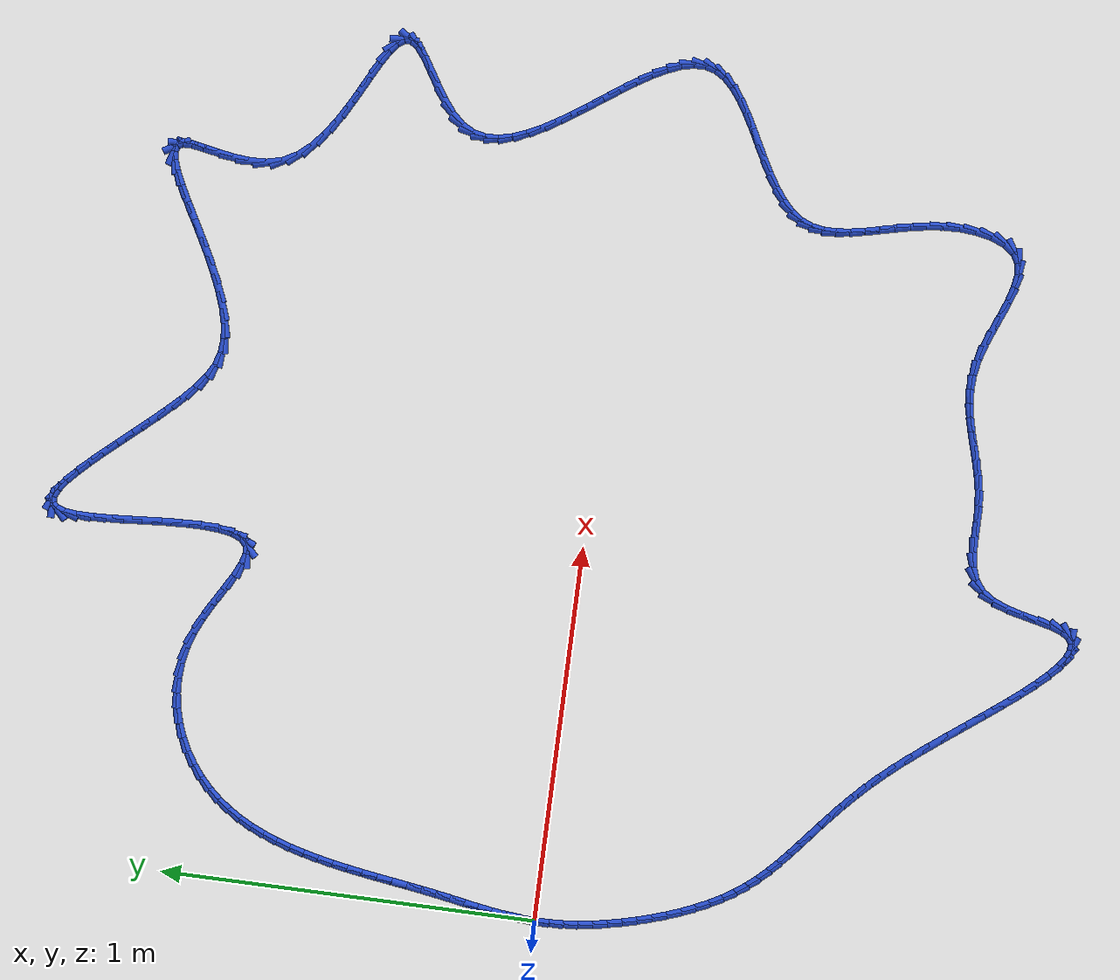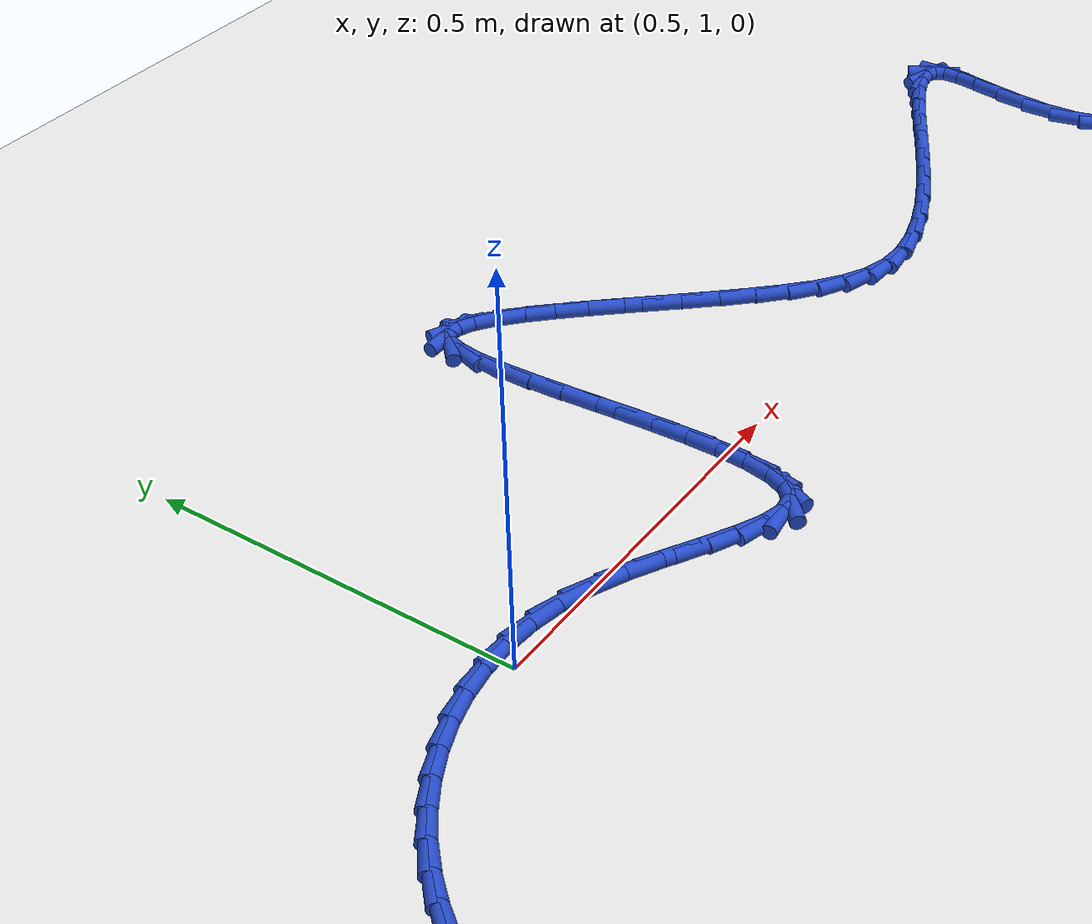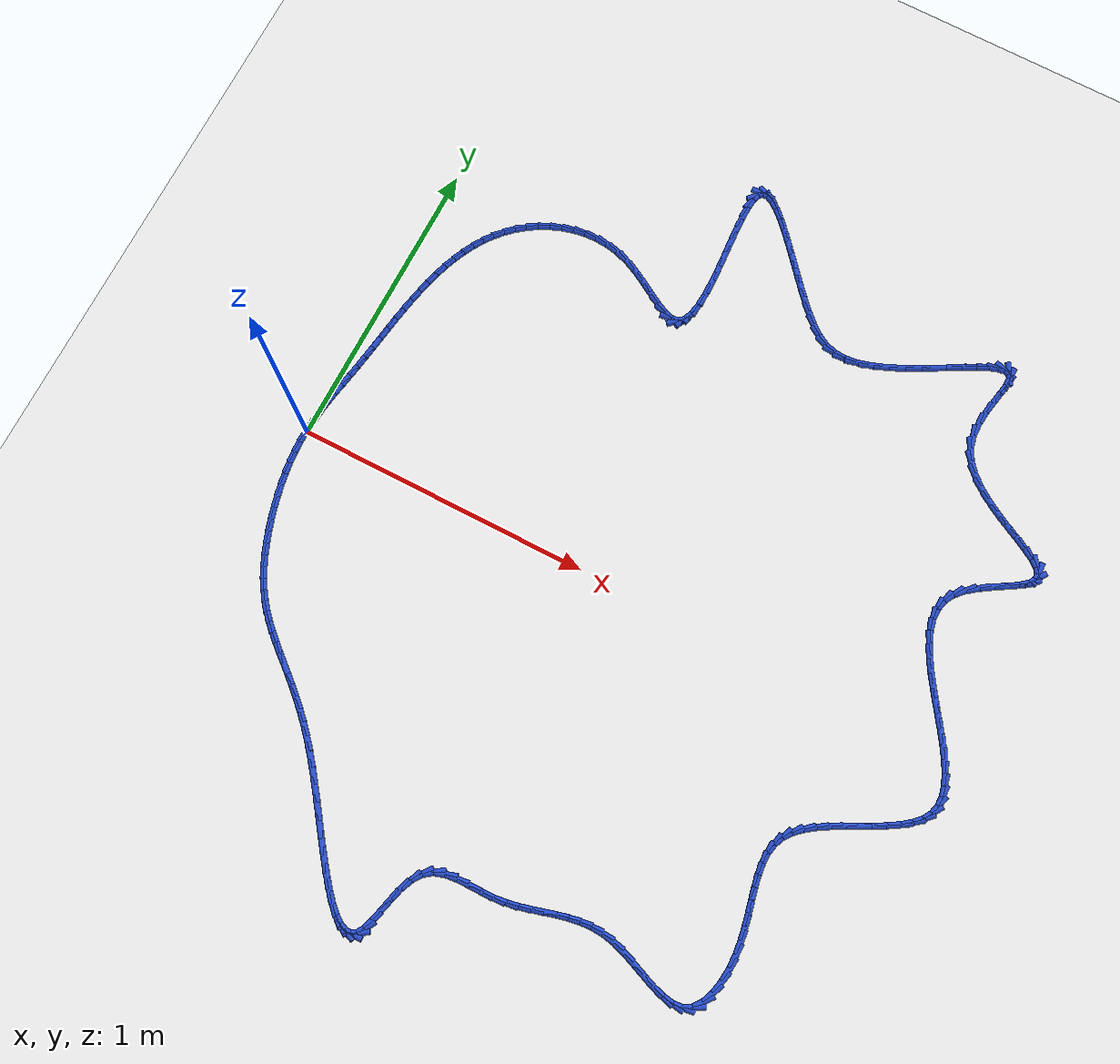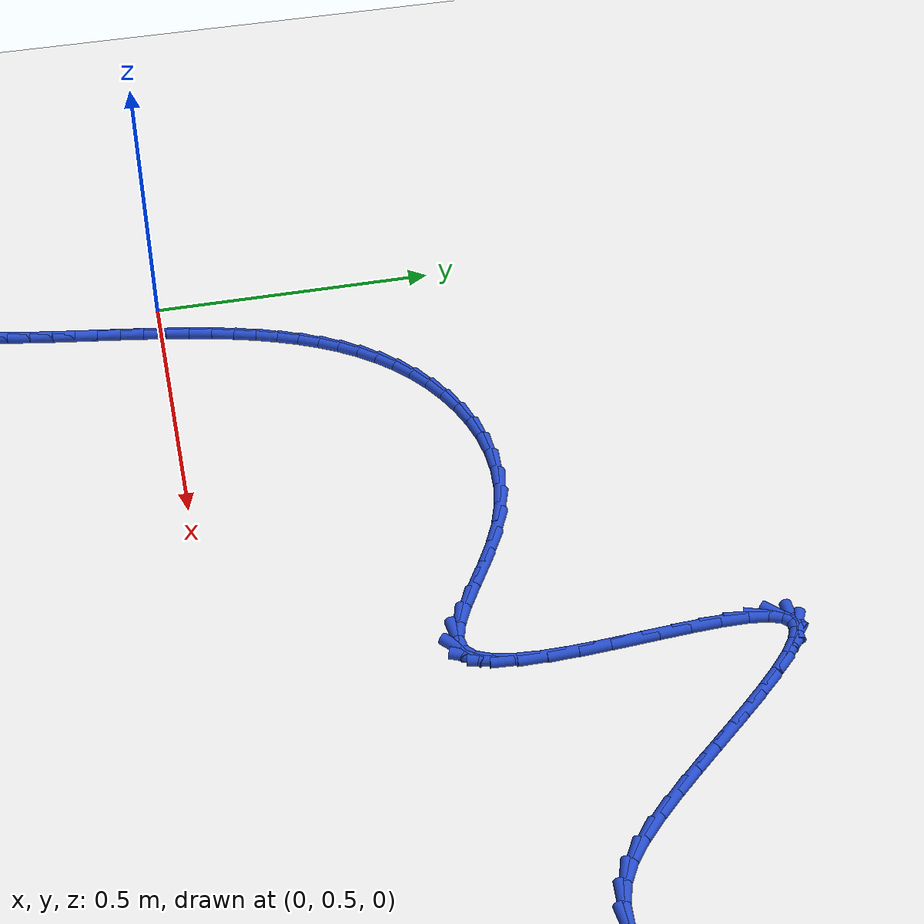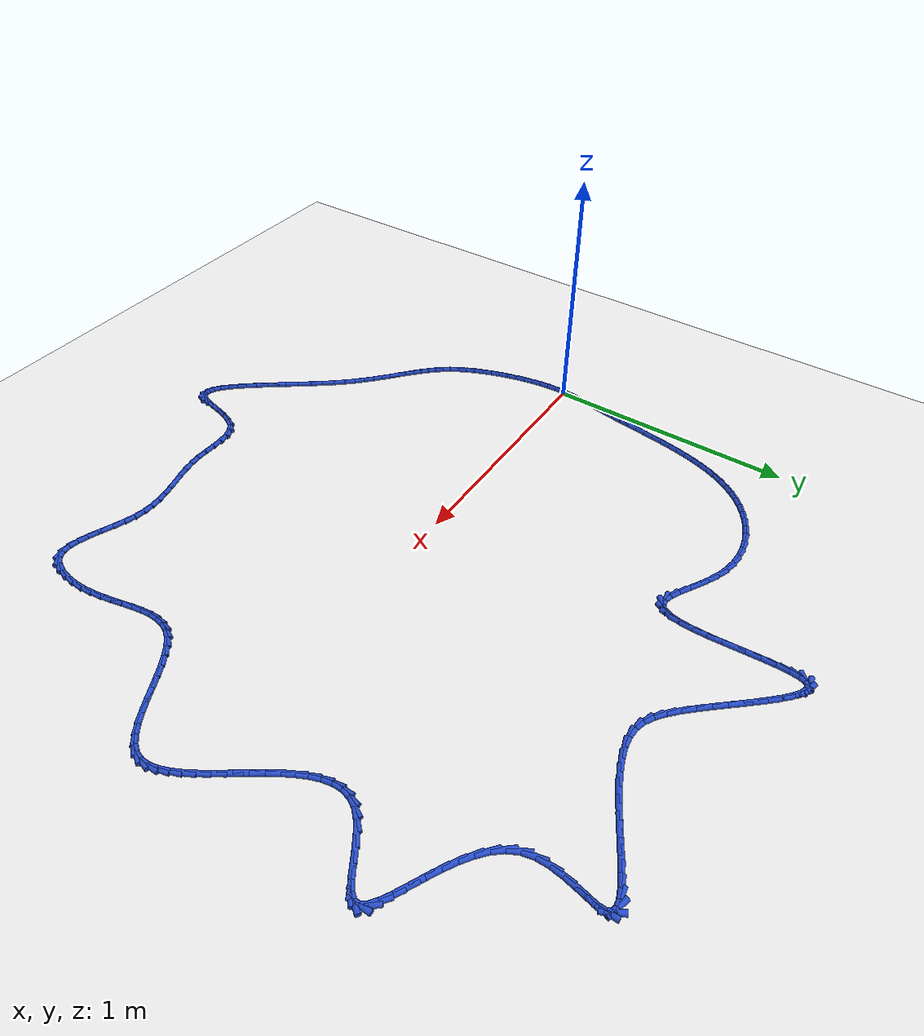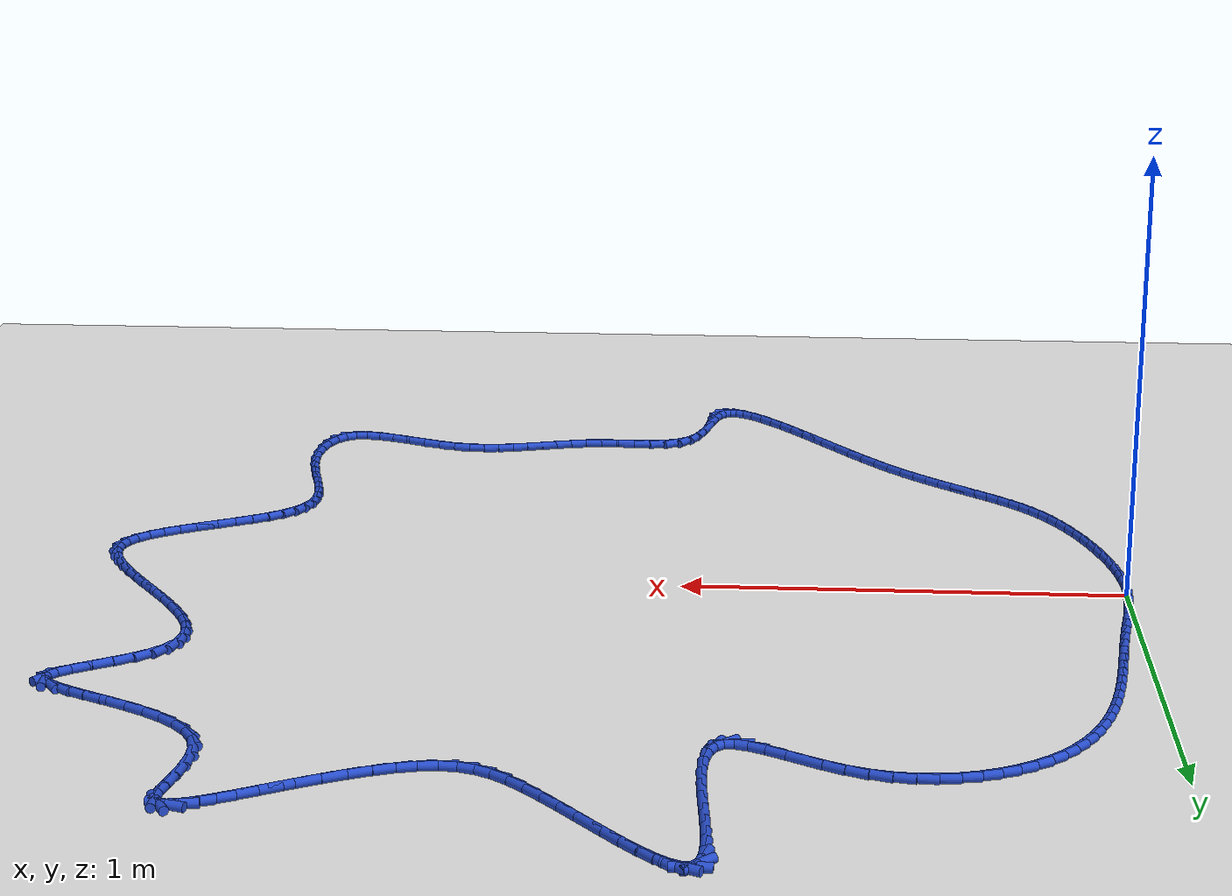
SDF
<sdf version="1.6">
 <world name="default">
  <light name="sun" type="directional">
   <pose>0 0 10 0 -0 0</pose>
   <diffuse>0.8 0.8 0.8 1</diffuse>
   <specular>0.2 0.2 0.2 1</specular>
   <attenuation>
    <range>1000</range>
    <constant>0.9</constant>
    <linear>0.01</linear>
    <quadratic>0.001</quadratic>
   </attenuation>
   <direction>-0.5 0.1 -0.9</direction>
  </light>
  <model name="ground_plane">
   <static>1</static>
   <link name="link">
    <collision name="collision">
     <geometry><plane><normal>0 0 1</normal><size>100 100</size></plane></geometry>
     <surface><friction><ode><mu>100</mu><mu2>50</mu2></ode></friction></surface>
    </collision>
    <visual name="visual">
     <cast_shadows>0</cast_shadows>
     <geometry><plane><normal>0 0 1</normal><size>100 100</size></plane></geometry>
     <material>
      <script><uri>file://media/materials/scripts/gazebo.material</uri><name>Gazebo/WhiteGlow</name></script>
     </material>
    </visual>
   </link>
  </model>
  <gravity>0 0 -9.8</gravity>
  <magnetic_field>6e-06 2.3e-05 -4.2e-05</magnetic_field>
  <atmosphere type="adiabatic"/>
  <physics name="default_physics" default="0" type="ode">
   <max_step_size>0.001</max_step_size>
   <real_time_factor>1</real_time_factor>
   <real_time_update_rate>1000</real_time_update_rate>
  </physics>
  <scene><ambient>0.4 0.4 0.4 1</ambient><background>0.7 0.7 0.7 1</background><shadows>1</shadows></scene>
  <spherical_coordinates>
   <surface_model>EARTH_WGS84</surface_model>
   <latitude_deg>0</latitude_deg>
   <longitude_deg>0</longitude_deg>
   <elevation>0</elevation>
   <heading_deg>0</heading_deg>
  </spherical_coordinates>
  <model name="line">
   <link name="link_0">
    <pose>0.0 -7.632783294297951e-17 0.01 0 1.57 1.5173744444518704</pose>
    <collision name="collision">
     <geometry><cylinder><radius>0.01</radius><length>0.08</length></cylinder></geometry>
    </collision>
    <visual name="visual">
     <material>
      <script><name>Gazebo/Blue</name><uri>file://media/materials/scripts/gazebo.material</uri></script>
     </material>
     <geometry><cylinder><radius>0.01</radius><length>0.08</length></cylinder></geometry>
    </visual>
   </link>
   <link name="link_1">
    <pose>0.002029088374936336 0.03794620572292945 0.01 0 1.57 1.473055200181778</pose>
    <collision name="collision">
     <geometry><cylinder><radius>0.01</radius><length>0.08</length></cylinder></geometry>
    </collision>
    <visual name="visual">
     <material>
      <script><name>Gazebo/Blue</name><uri>file://media/materials/scripts/gazebo.material</uri></script>
     </material>
     <geometry><cylinder><radius>0.01</radius><length>0.08</length></cylinder></geometry>
    </visual>
   </link>
   <link name="link_2">
    <pose>0.005744953741146167 0.07584248328195795 0.01 0 1.57 1.4388416482292508</pose>
    <collision name="collision">
     <geometry><cylinder><radius>0.01</radius><length>0.08</length></cylinder></geometry>
    </collision>
    <visual name="visual">
     <material>
      <script><name>Gazebo/Blue</name><uri>file://media/materials/scripts/gazebo.material</uri></script>
     </material>
     <geometry><cylinder><radius>0.01</radius><length>0.08</length></cylinder></geometry>
    </visual>
   </link>
   <link name="link_3">
    <pose>0.010782486546239103 0.11379688520892949 0.01 0 1.57 1.4148330465332677</pose>
    <collision name="collision">
     <geometry><cylinder><radius>0.01</radius><length>0.08</length></cylinder></geometry>
    </collision>
    <visual name="visual">
     <material>
      <script><name>Gazebo/Blue</name><uri>file://media/materials/scripts/gazebo.material</uri></script>
     </material>
     <geometry><cylinder><radius>0.01</radius><length>0.08</length></cylinder></geometry>
    </visual>
   </link>
   <link name="link_4">
    <pose>0.01677657723782473 0.15191746403568815 0.01 0 1.57 1.4009276794443999</pose>
    <collision name="collision">
     <geometry><cylinder><radius>0.01</radius><length>0.08</length></cylinder></geometry>
    </collision>
    <visual name="visual">
     <material>
      <script><name>Gazebo/Blue</name><uri>file://media/materials/scripts/gazebo.material</uri></script>
     </material>
     <geometry><cylinder><radius>0.01</radius><length>0.08</length></cylinder></geometry>
    </visual>
   </link>
   <link name="link_5">
    <pose>0.023362116263512634 0.19031227229407793 0.01 0 1.57 1.3969029857546884</pose>
    <collision name="collision">
     <geometry><cylinder><radius>0.01</radius><length>0.08</length></cylinder></geometry>
    </collision>
    <visual name="visual">
     <material>
      <script><name>Gazebo/Blue</name><uri>file://media/materials/scripts/gazebo.material</uri></script>
     </material>
     <geometry><cylinder><radius>0.01</radius><length>0.08</length></cylinder></geometry>
    </visual>
   </link>
   <link name="link_6">
    <pose>0.030173994070912438 0.22908936251594303 0.01 0 1.57 1.4024644631420349</pose>
    <collision name="collision">
     <geometry><cylinder><radius>0.01</radius><length>0.08</length></cylinder></geometry>
    </collision>
    <visual name="visual">
     <material>
      <script><name>Gazebo/Blue</name><uri>file://media/materials/scripts/gazebo.material</uri></script>
     </material>
     <geometry><cylinder><radius>0.01</radius><length>0.08</length></cylinder></geometry>
    </visual>
   </link>
   <link name="link_7">
    <pose>0.03684710110763371 0.26835678723312734 0.01 0 1.57 1.4150594093517095</pose>
    <collision name="collision">
     <geometry><cylinder><radius>0.01</radius><length>0.08</length></cylinder></geometry>
    </collision>
    <visual name="visual">
     <material>
      <script><name>Gazebo/Blue</name><uri>file://media/materials/scripts/gazebo.material</uri></script>
     </material>
     <geometry><cylinder><radius>0.01</radius><length>0.08</length></cylinder></geometry>
    </visual>
   </link>
   <link name="link_8">
    <pose>0.04310015686612746 0.30818305375736876 0.01 0 1.57 1.4247196766114751</pose>
    <collision name="collision">
     <geometry><cylinder><radius>0.01</radius><length>0.08</length></cylinder></geometry>
    </collision>
    <visual name="visual">
     <material>
      <script><name>Gazebo/Blue</name><uri>file://media/materials/scripts/gazebo.material</uri></script>
     </material>
     <geometry><cylinder><radius>0.01</radius><length>0.08</length></cylinder></geometry>
    </visual>
   </link>
   <link name="link_9">
    <pose>0.04902591946348311 0.34846022172922536 0.01 0 1.57 1.4289074277176792</pose>
    <collision name="collision">
     <geometry><cylinder><radius>0.01</radius><length>0.08</length></cylinder></geometry>
    </collision>
    <visual name="visual">
     <material>
      <script><name>Gazebo/Blue</name><uri>file://media/materials/scripts/gazebo.material</uri></script>
     </material>
     <geometry><cylinder><radius>0.01</radius><length>0.08</length></cylinder></geometry>
    </visual>
   </link>
   <link name="link_10">
    <pose>0.05482142970664274 0.3890311568382645 0.01 0 1.57 1.4277694946308872</pose>
    <collision name="collision">
     <geometry><cylinder><radius>0.01</radius><length>0.08</length></cylinder></geometry>
    </collision>
    <visual name="visual">
     <material>
      <script><name>Gazebo/Blue</name><uri>file://media/materials/scripts/gazebo.material</uri></script>
     </material>
     <geometry><cylinder><radius>0.01</radius><length>0.08</length></cylinder></geometry>
    </visual>
   </link>
   <link name="link_11">
    <pose>0.06068373292136278 0.4297387226423643 0.01 0 1.57 1.4213515911380894</pose>
    <collision name="collision">
     <geometry><cylinder><radius>0.01</radius><length>0.08</length></cylinder></geometry>
    </collision>
    <visual name="visual">
     <material>
      <script><name>Gazebo/Blue</name><uri>file://media/materials/scripts/gazebo.material</uri></script>
     </material>
     <geometry><cylinder><radius>0.01</radius><length>0.08</length></cylinder></geometry>
    </visual>
   </link>
   <link name="link_12">
    <pose>0.06680987443339961 0.4704257826994027 0.01 0 1.57 1.4096023358931709</pose>
    <collision name="collision">
     <geometry><cylinder><radius>0.01</radius><length>0.08</length></cylinder></geometry>
    </collision>
    <visual name="visual">
     <material>
      <script><name>Gazebo/Blue</name><uri>file://media/materials/scripts/gazebo.material</uri></script>
     </material>
     <geometry><cylinder><radius>0.01</radius><length>0.08</length></cylinder></geometry>
    </visual>
   </link>
   <link name="link_13">
    <pose>0.07339689956850962 0.5109352005672576 0.01 0 1.57 1.3923774619848166</pose>
    <collision name="collision">
     <geometry><cylinder><radius>0.01</radius><length>0.08</length></cylinder></geometry>
    </collision>
    <visual name="visual">
     <material>
      <script><name>Gazebo/Blue</name><uri>file://media/materials/scripts/gazebo.material</uri></script>
     </material>
     <geometry><cylinder><radius>0.01</radius><length>0.08</length></cylinder></geometry>
    </visual>
   </link>
   <link name="link_14">
    <pose>0.0806418536524492 0.5511098398038071 0.01 0 1.57 1.3694450295526541</pose>
    <collision name="collision">
     <geometry><cylinder><radius>0.01</radius><length>0.08</length></cylinder></geometry>
    </collision>
    <visual name="visual">
     <material>
      <script><name>Gazebo/Blue</name><uri>file://media/materials/scripts/gazebo.material</uri></script>
     </material>
     <geometry><cylinder><radius>0.01</radius><length>0.08</length></cylinder></geometry>
    </visual>
   </link>
   <link name="link_15">
    <pose>0.08874178201097477 0.5907925639669293 0.01 0 1.57 1.340493421312759</pose>
    <collision name="collision">
     <geometry><cylinder><radius>0.01</radius><length>0.08</length></cylinder></geometry>
    </collision>
    <visual name="visual">
     <material>
      <script><name>Gazebo/Blue</name><uri>file://media/materials/scripts/gazebo.material</uri></script>
     </material>
     <geometry><cylinder><radius>0.01</radius><length>0.08</length></cylinder></geometry>
    </visual>
   </link>
   <link name="link_16">
    <pose>0.09789372996984268 0.6298262366145019 0.01 0 1.57 1.305144917619309</pose>
    <collision name="collision">
     <geometry><cylinder><radius>0.01</radius><length>0.08</length></cylinder></geometry>
    </collision>
    <visual name="visual">
     <material>
      <script><name>Gazebo/Blue</name><uri>file://media/materials/scripts/gazebo.material</uri></script>
     </material>
     <geometry><cylinder><radius>0.01</radius><length>0.08</length></cylinder></geometry>
    </visual>
   </link>
   <link name="link_17">
    <pose>0.10829474285480936 0.6680537213044031 0.01 0 1.57 1.2629788435202836</pose>
    <collision name="collision">
     <geometry><cylinder><radius>0.01</radius><length>0.08</length></cylinder></geometry>
    </collision>
    <visual name="visual">
     <material>
      <script><name>Gazebo/Blue</name><uri>file://media/materials/scripts/gazebo.material</uri></script>
     </material>
     <geometry><cylinder><radius>0.01</radius><length>0.08</length></cylinder></geometry>
    </visual>
   </link>
   <link name="link_18">
    <pose>0.12014186599163118 0.7053178815945107 0.01 0 1.57 1.213569457138185</pose>
    <collision name="collision">
     <geometry><cylinder><radius>0.01</radius><length>0.08</length></cylinder></geometry>
    </collision>
    <visual name="visual">
     <material>
      <script><name>Gazebo/Blue</name><uri>file://media/materials/scripts/gazebo.material</uri></script>
     </material>
     <geometry><cylinder><radius>0.01</radius><length>0.08</length></cylinder></geometry>
    </visual>
   </link>
   <link name="link_19">
    <pose>0.1336321447060645 0.7414615810427028 0.01 0 1.57 1.1565443175918892</pose>
    <collision name="collision">
     <geometry><cylinder><radius>0.01</radius><length>0.08</length></cylinder></geometry>
    </collision>
    <visual name="visual">
     <material>
      <script><name>Gazebo/Blue</name><uri>file://media/materials/scripts/gazebo.material</uri></script>
     </material>
     <geometry><cylinder><radius>0.01</radius><length>0.08</length></cylinder></geometry>
    </visual>
   </link>
   <link name="link_20">
    <pose>0.14896262432386578 0.7763276832068573 0.01 0 1.57 1.0916676313626663</pose>
    <collision name="collision">
     <geometry><cylinder><radius>0.01</radius><length>0.08</length></cylinder></geometry>
    </collision>
    <visual name="visual">
     <material>
      <script><name>Gazebo/Blue</name><uri>file://media/materials/scripts/gazebo.material</uri></script>
     </material>
     <geometry><cylinder><radius>0.01</radius><length>0.08</length></cylinder></geometry>
    </visual>
   </link>
   <link name="link_21">
    <pose>0.16633035017079137 0.8097590516448523 0.01 0 1.57 1.0189481878904165</pose>
    <collision name="collision">
     <geometry><cylinder><radius>0.01</radius><length>0.08</length></cylinder></geometry>
    </collision>
    <visual name="visual">
     <material>
      <script><name>Gazebo/Blue</name><uri>file://media/materials/scripts/gazebo.material</uri></script>
     </material>
     <geometry><cylinder><radius>0.01</radius><length>0.08</length></cylinder></geometry>
    </visual>
   </link>
   <link name="link_22">
    <pose>0.18593236757259768 0.8415985499145657 0.01 0 1.57 0.9387611671702188</pose>
    <collision name="collision">
     <geometry><cylinder><radius>0.01</radius><length>0.08</length></cylinder></geometry>
    </collision>
    <visual name="visual">
     <material>
      <script><name>Gazebo/Blue</name><uri>file://media/materials/scripts/gazebo.material</uri></script>
     </material>
     <geometry><cylinder><radius>0.01</radius><length>0.08</length></cylinder></geometry>
    </visual>
   </link>
   <link name="link_23">
    <pose>0.20796572185504109 0.8716890415738756 0.01 0 1.57 0.8519576569823705</pose>
    <collision name="collision">
     <geometry><cylinder><radius>0.01</radius><length>0.08</length></cylinder></geometry>
    </collision>
    <visual name="visual">
     <material>
      <script><name>Gazebo/Blue</name><uri>file://media/materials/scripts/gazebo.material</uri></script>
     </material>
     <geometry><cylinder><radius>0.01</radius><length>0.08</length></cylinder></geometry>
    </visual>
   </link>
   <link name="link_24">
    <pose>0.23262745834387805 0.8998733901806598 0.01 0 1.57 0.7599669564312679</pose>
    <collision name="collision">
     <geometry><cylinder><radius>0.01</radius><length>0.08</length></cylinder></geometry>
    </collision>
    <visual name="visual">
     <material>
      <script><name>Gazebo/Blue</name><uri>file://media/materials/scripts/gazebo.material</uri></script>
     </material>
     <geometry><cylinder><radius>0.01</radius><length>0.08</length></cylinder></geometry>
    </visual>
   </link>
   <link name="link_25">
    <pose>0.2601096772268201 0.9259921768534706 0.01 0 1.57 0.6659326873562499</pose>
    <collision name="collision">
     <geometry><cylinder><radius>0.01</radius><length>0.08</length></cylinder></geometry>
    </collision>
    <visual name="visual">
     <material>
      <script><name>Gazebo/Blue</name><uri>file://media/materials/scripts/gazebo.material</uri></script>
     </material>
     <geometry><cylinder><radius>0.01</radius><length>0.08</length></cylinder></geometry>
    </visual>
   </link>
   <link name="link_26">
    <pose>0.2904051819307278 0.9497939968531709 0.01 0 1.57 0.5713707651524974</pose>
    <collision name="collision">
     <geometry><cylinder><radius>0.01</radius><length>0.08</length></cylinder></geometry>
    </collision>
    <visual name="visual">
     <material>
      <script><name>Gazebo/Blue</name><uri>file://media/materials/scripts/gazebo.material</uri></script>
     </material>
     <geometry><cylinder><radius>0.01</radius><length>0.08</length></cylinder></geometry>
    </visual>
   </link>
   <link name="link_27">
    <pose>0.3232437256136845 0.970906034011327 0.01 0 1.57 0.4748559088709287</pose>
    <collision name="collision">
     <geometry><cylinder><radius>0.01</radius><length>0.08</length></cylinder></geometry>
    </collision>
    <visual name="visual">
     <material>
      <script><name>Gazebo/Blue</name><uri>file://media/materials/scripts/gazebo.material</uri></script>
     </material>
     <geometry><cylinder><radius>0.01</radius><length>0.08</length></cylinder></geometry>
    </visual>
   </link>
   <link name="link_28">
    <pose>0.3583370568904822 0.9889471621230053 0.01 0 1.57 0.3750314027690819</pose>
    <collision name="collision">
     <geometry><cylinder><radius>0.01</radius><length>0.08</length></cylinder></geometry>
    </collision>
    <visual name="visual">
     <material>
      <script><name>Gazebo/Blue</name><uri>file://media/materials/scripts/gazebo.material</uri></script>
     </material>
     <geometry><cylinder><radius>0.01</radius><length>0.08</length></cylinder></geometry>
    </visual>
   </link>
   <link name="link_29">
    <pose>0.3953969243759126 1.0035362549832727 0.01 0 1.57 0.27083501432303775</pose>
    <collision name="collision">
     <geometry><cylinder><radius>0.01</radius><length>0.08</length></cylinder></geometry>
    </collision>
    <visual name="visual">
     <material>
      <script><name>Gazebo/Blue</name><uri>file://media/materials/scripts/gazebo.material</uri></script>
     </material>
     <geometry><cylinder><radius>0.01</radius><length>0.08</length></cylinder></geometry>
    </visual>
   </link>
   <link name="link_30">
    <pose>0.43413507668476786 1.014292186387196 0.01 0 1.57 0.16159719585058546</pose>
    <collision name="collision">
     <geometry><cylinder><radius>0.01</radius><length>0.08</length></cylinder></geometry>
    </collision>
    <visual name="visual">
     <material>
      <script><name>Gazebo/Blue</name><uri>file://media/materials/scripts/gazebo.material</uri></script>
     </material>
     <geometry><cylinder><radius>0.01</radius><length>0.08</length></cylinder></geometry>
    </visual>
   </link>
   <link name="link_31">
    <pose>0.4742632624318398 1.0208338301298416 0.01 0 1.57 0.047169240069005365</pose>
    <collision name="collision">
     <geometry><cylinder><radius>0.01</radius><length>0.08</length></cylinder></geometry>
    </collision>
    <visual name="visual">
     <material>
      <script><name>Gazebo/Blue</name><uri>file://media/materials/scripts/gazebo.material</uri></script>
     </material>
     <geometry><cylinder><radius>0.01</radius><length>0.08</length></cylinder></geometry>
    </visual>
   </link>
   <link name="link_32">
    <pose>0.5154932302319205 1.0227800600062762 0.01 0 1.57 -0.07195117491863527</pose>
    <collision name="collision">
     <geometry><cylinder><radius>0.01</radius><length>0.08</length></cylinder></geometry>
    </collision>
    <visual name="visual">
     <material>
      <script><name>Gazebo/Blue</name><uri>file://media/materials/scripts/gazebo.material</uri></script>
     </material>
     <geometry><cylinder><radius>0.01</radius><length>0.08</length></cylinder></geometry>
    </visual>
   </link>
   <link name="link_33">
    <pose>0.5575367286998016 1.0197497498115666 0.01 0 1.57 -0.1945528694359533</pose>
    <collision name="collision">
     <geometry><cylinder><radius>0.01</radius><length>0.08</length></cylinder></geometry>
    </collision>
    <visual name="visual">
     <material>
      <script><name>Gazebo/Blue</name><uri>file://media/materials/scripts/gazebo.material</uri></script>
     </material>
     <geometry><cylinder><radius>0.01</radius><length>0.08</length></cylinder></geometry>
    </visual>
   </link>
   <link name="link_34">
    <pose>0.6001055064502753 1.0113617733407794 0.01 0 1.57 -0.3187642740556319</pose>
    <collision name="collision">
     <geometry><cylinder><radius>0.01</radius><length>0.08</length></cylinder></geometry>
    </collision>
    <visual name="visual">
     <material>
      <script><name>Gazebo/Blue</name><uri>file://media/materials/scripts/gazebo.material</uri></script>
     </material>
     <geometry><cylinder><radius>0.01</radius><length>0.08</length></cylinder></geometry>
    </visual>
   </link>
   <link name="link_35">
    <pose>0.6429112991122647 0.9972350684060942 0.01 0 1.57 -0.43166994559678284</pose>
    <collision name="collision">
     <geometry><cylinder><radius>0.01</radius><length>0.08</length></cylinder></geometry>
    </collision>
    <visual name="visual">
     <material>
      <script><name>Gazebo/Blue</name><uri>file://media/materials/scripts/gazebo.material</uri></script>
     </material>
     <geometry><cylinder><radius>0.01</radius><length>0.08</length></cylinder></geometry>
    </visual>
   </link>
   <link name="link_36">
    <pose>0.6855423541859551 0.9775973386826077 0.01 0 1.57 -0.501572258225648</pose>
    <collision name="collision">
     <geometry><cylinder><radius>0.01</radius><length>0.08</length></cylinder></geometry>
    </collision>
    <visual name="visual">
     <material>
      <script><name>Gazebo/Blue</name><uri>file://media/materials/scripts/gazebo.material</uri></script>
     </material>
     <geometry><cylinder><radius>0.01</radius><length>0.08</length></cylinder></geometry>
    </visual>
   </link>
   <link name="link_37">
    <pose>0.7271610073528116 0.954775927531406 0.01 0 1.57 -0.529588721069814</pose>
    <collision name="collision">
     <geometry><cylinder><radius>0.01</radius><length>0.08</length></cylinder></geometry>
    </collision>
    <visual name="visual">
     <material>
      <script><name>Gazebo/Blue</name><uri>file://media/materials/scripts/gazebo.material</uri></script>
     </material>
     <geometry><cylinder><radius>0.01</radius><length>0.08</length></cylinder></geometry>
    </visual>
   </link>
   <link name="link_38">
    <pose>0.7668378383802582 0.931550512224219 0.01 0 1.57 -0.5154100114677903</pose>
    <collision name="collision">
     <geometry><cylinder><radius>0.01</radius><length>0.08</length></cylinder></geometry>
    </collision>
    <visual name="visual">
     <material>
      <script><name>Gazebo/Blue</name><uri>file://media/materials/scripts/gazebo.material</uri></script>
     </material>
     <geometry><cylinder><radius>0.01</radius><length>0.08</length></cylinder></geometry>
    </visual>
   </link>
   <link name="link_39">
    <pose>0.8036434270357179 0.9107007700327749 0.01 0 1.57 -0.443869790424349</pose>
    <collision name="collision">
     <geometry><cylinder><radius>0.01</radius><length>0.08</length></cylinder></geometry>
    </collision>
    <visual name="visual">
     <material>
      <script><name>Gazebo/Blue</name><uri>file://media/materials/scripts/gazebo.material</uri></script>
     </material>
     <geometry><cylinder><radius>0.01</radius><length>0.08</length></cylinder></geometry>
    </visual>
   </link>
   <link name="link_40">
    <pose>0.8366483530866142 0.8950063782288026 0.01 0 1.57 -0.2678328847738722</pose>
    <collision name="collision">
     <geometry><cylinder><radius>0.01</radius><length>0.08</length></cylinder></geometry>
    </collision>
    <visual name="visual">
     <material>
      <script><name>Gazebo/Blue</name><uri>file://media/materials/scripts/gazebo.material</uri></script>
     </material>
     <geometry><cylinder><radius>0.01</radius><length>0.08</length></cylinder></geometry>
    </visual>
   </link>
   <link name="link_41">
    <pose>0.86492319630037 0.8872470140840307 0.01 0 1.57 0.1298252275558873</pose>
    <collision name="collision">
     <geometry><cylinder><radius>0.01</radius><length>0.08</length></cylinder></geometry>
    </collision>
    <visual name="visual">
     <material>
      <script><name>Gazebo/Blue</name><uri>file://media/materials/scripts/gazebo.material</uri></script>
     </material>
     <geometry><cylinder><radius>0.01</radius><length>0.08</length></cylinder></geometry>
    </visual>
   </link>
   <link name="link_42">
    <pose>0.8875395206252846 0.8901997914902295 0.01 0 1.57 0.7476197615415479</pose>
    <collision name="collision">
     <geometry><cylinder><radius>0.01</radius><length>0.08</length></cylinder></geometry>
    </collision>
    <visual name="visual">
     <material>
      <script><name>Gazebo/Blue</name><uri>file://media/materials/scripts/gazebo.material</uri></script>
     </material>
     <geometry><cylinder><radius>0.01</radius><length>0.08</length></cylinder></geometry>
    </visual>
   </link>
   <link name="link_43">
    <pose>0.9040163285786222 0.9054764338221941 0.01 0 1.57 1.173080980686533</pose>
    <collision name="collision">
     <geometry><cylinder><radius>0.01</radius><length>0.08</length></cylinder></geometry>
    </collision>
    <visual name="visual">
     <material>
      <script><name>Gazebo/Blue</name><uri>file://media/materials/scripts/gazebo.material</uri></script>
     </material>
     <geometry><cylinder><radius>0.01</radius><length>0.08</length></cylinder></geometry>
    </visual>
   </link>
   <link name="link_44">
    <pose>0.9150262153935563 0.9316840374403654 0.01 0 1.57 1.39131081522536</pose>
    <collision name="collision">
     <geometry><cylinder><radius>0.01</radius><length>0.08</length></cylinder></geometry>
    </collision>
    <visual name="visual">
     <material>
      <script><name>Gazebo/Blue</name><uri>file://media/materials/scripts/gazebo.material</uri></script>
     </material>
     <geometry><cylinder><radius>0.01</radius><length>0.08</length></cylinder></geometry>
    </visual>
   </link>
   <link name="link_45">
    <pose>0.9214251714929196 0.9669520308649239 0.01 0 1.57 1.5086026866258215</pose>
    <collision name="collision">
     <geometry><cylinder><radius>0.01</radius><length>0.08</length></cylinder></geometry>
    </collision>
    <visual name="visual">
     <material>
      <script><name>Gazebo/Blue</name><uri>file://media/materials/scripts/gazebo.material</uri></script>
     </material>
     <geometry><cylinder><radius>0.01</radius><length>0.08</length></cylinder></geometry>
    </visual>
   </link>
   <link name="link_46">
    <pose>0.9240691872995446 1.0094098426160492 0.01 0 1.57 -1.5654604678844504</pose>
    <collision name="collision">
     <geometry><cylinder><radius>0.01</radius><length>0.08</length></cylinder></geometry>
    </collision>
    <visual name="visual">
     <material>
      <script><name>Gazebo/Blue</name><uri>file://media/materials/scripts/gazebo.material</uri></script>
     </material>
     <geometry><cylinder><radius>0.01</radius><length>0.08</length></cylinder></geometry>
    </visual>
   </link>
   <link name="link_47">
    <pose>0.9238142532362632 1.0571869012139212 0.01 0 1.57 -1.5259681930906963</pose>
    <collision name="collision">
     <geometry><cylinder><radius>0.01</radius><length>0.08</length></cylinder></geometry>
    </collision>
    <visual name="visual">
     <material>
      <script><name>Gazebo/Blue</name><uri>file://media/materials/scripts/gazebo.material</uri></script>
     </material>
     <geometry><cylinder><radius>0.01</radius><length>0.08</length></cylinder></geometry>
    </visual>
   </link>
   <link name="link_48">
    <pose>0.9215163597259078 1.1084126351787202 0.01 0 1.57 -1.5048955061222342</pose>
    <collision name="collision">
     <geometry><cylinder><radius>0.01</radius><length>0.08</length></cylinder></geometry>
    </collision>
    <visual name="visual">
     <material>
      <script><name>Gazebo/Blue</name><uri>file://media/materials/scripts/gazebo.material</uri></script>
     </material>
     <geometry><cylinder><radius>0.01</radius><length>0.08</length></cylinder></geometry>
    </visual>
   </link>
   <link name="link_49">
    <pose>0.918031497191311 1.1612164730306254 0.01 0 1.57 -1.498256878310859</pose>
    <collision name="collision">
     <geometry><cylinder><radius>0.01</radius><length>0.08</length></cylinder></geometry>
    </collision>
    <visual name="visual">
     <material>
      <script><name>Gazebo/Blue</name><uri>file://media/materials/scripts/gazebo.material</uri></script>
     </material>
     <geometry><cylinder><radius>0.01</radius><length>0.08</length></cylinder></geometry>
    </visual>
   </link>
   <link name="link_50">
    <pose>0.9142156560553051 1.2137278432898178 0.01 0 1.57 -1.5055279262098844</pose>
    <collision name="collision">
     <geometry><cylinder><radius>0.01</radius><length>0.08</length></cylinder></geometry>
    </collision>
    <visual name="visual">
     <material>
      <script><name>Gazebo/Blue</name><uri>file://media/materials/scripts/gazebo.material</uri></script>
     </material>
     <geometry><cylinder><radius>0.01</radius><length>0.08</length></cylinder></geometry>
    </visual>
   </link>
   <link name="link_51">
    <pose>0.9109248267407226 1.2640761744764766 0.01 0 1.57 -1.529583821137753</pose>
    <collision name="collision">
     <geometry><cylinder><radius>0.01</radius><length>0.08</length></cylinder></geometry>
    </collision>
    <visual name="visual">
     <material>
      <script><name>Gazebo/Blue</name><uri>file://media/materials/scripts/gazebo.material</uri></script>
     </material>
     <geometry><cylinder><radius>0.01</radius><length>0.08</length></cylinder></geometry>
    </visual>
   </link>
   <link name="link_52">
    <pose>0.9090149996703953 1.3103908951107823 0.01 0 1.57 1.5627004572462482</pose>
    <collision name="collision">
     <geometry><cylinder><radius>0.01</radius><length>0.08</length></cylinder></geometry>
    </collision>
    <visual name="visual">
     <material>
      <script><name>Gazebo/Blue</name><uri>file://media/materials/scripts/gazebo.material</uri></script>
     </material>
     <geometry><cylinder><radius>0.01</radius><length>0.08</length></cylinder></geometry>
    </visual>
   </link>
   <link name="link_53">
    <pose>0.9093421652671563 1.3508014337129146 0.01 0 1.57 1.4663799651946237</pose>
    <collision name="collision">
     <geometry><cylinder><radius>0.01</radius><length>0.08</length></cylinder></geometry>
    </collision>
    <visual name="visual">
     <material>
      <script><name>Gazebo/Blue</name><uri>file://media/materials/scripts/gazebo.material</uri></script>
     </material>
     <geometry><cylinder><radius>0.01</radius><length>0.08</length></cylinder></geometry>
    </visual>
   </link>
   <link name="link_54">
    <pose>0.9127623139538374 1.3834372188030535 0.01 0 1.57 1.2606130804991729</pose>
    <collision name="collision">
     <geometry><cylinder><radius>0.01</radius><length>0.08</length></cylinder></geometry>
    </collision>
    <visual name="visual">
     <material>
      <script><name>Gazebo/Blue</name><uri>file://media/materials/scripts/gazebo.material</uri></script>
     </material>
     <geometry><cylinder><radius>0.01</radius><length>0.08</length></cylinder></geometry>
    </visual>
   </link>
   <link name="link_55">
    <pose>0.9201314361532713 1.4064276789013785 0.01 0 1.57 0.7622477372073089</pose>
    <collision name="collision">
     <geometry><cylinder><radius>0.01</radius><length>0.08</length></cylinder></geometry>
    </collision>
    <visual name="visual">
     <material>
      <script><name>Gazebo/Blue</name><uri>file://media/materials/scripts/gazebo.material</uri></script>
     </material>
     <geometry><cylinder><radius>0.01</radius><length>0.08</length></cylinder></geometry>
    </visual>
   </link>
   <link name="link_56">
    <pose>0.9322600594828168 1.41800734710478 0.01 0 1.57 0.008740368043914565</pose>
    <collision name="collision">
     <geometry><cylinder><radius>0.01</radius><length>0.08</length></cylinder></geometry>
    </collision>
    <visual name="visual">
     <material>
      <script><name>Gazebo/Blue</name><uri>file://media/materials/scripts/gazebo.material</uri></script>
     </material>
     <geometry><cylinder><radius>0.01</radius><length>0.08</length></cylinder></geometry>
    </visual>
   </link>
   <link name="link_57">
    <pose>0.9492040484138605 1.4181554475755194 0.01 0 1.57 -0.4357348969624494</pose>
    <collision name="collision">
     <geometry><cylinder><radius>0.01</radius><length>0.08</length></cylinder></geometry>
    </collision>
    <visual name="visual">
     <material>
      <script><name>Gazebo/Blue</name><uri>file://media/materials/scripts/gazebo.material</uri></script>
     </material>
     <geometry><cylinder><radius>0.01</radius><length>0.08</length></cylinder></geometry>
    </visual>
   </link>
   <link name="link_58">
    <pose>0.9703977532435921 1.4082880710202343 0.01 0 1.57 -0.6378004394428387</pose>
    <collision name="collision">
     <geometry><cylinder><radius>0.01</radius><length>0.08</length></cylinder></geometry>
    </collision>
    <visual name="visual">
     <material>
      <script><name>Gazebo/Blue</name><uri>file://media/materials/scripts/gazebo.material</uri></script>
     </material>
     <geometry><cylinder><radius>0.01</radius><length>0.08</length></cylinder></geometry>
    </visual>
   </link>
   <link name="link_59">
    <pose>0.9952570061976413 1.3898641197154311 0.01 0 1.57 -0.740181951555538</pose>
    <collision name="collision">
     <geometry><cylinder><radius>0.01</radius><length>0.08</length></cylinder></geometry>
    </collision>
    <visual name="visual">
     <material>
      <script><name>Gazebo/Blue</name><uri>file://media/materials/scripts/gazebo.material</uri></script>
     </material>
     <geometry><cylinder><radius>0.01</radius><length>0.08</length></cylinder></geometry>
    </visual>
   </link>
   <link name="link_60">
    <pose>1.0231976395016364 1.3643424959376165 0.01 0 1.57 -0.797127637485828</pose>
    <collision name="collision">
     <geometry><cylinder><radius>0.01</radius><length>0.08</length></cylinder></geometry>
    </collision>
    <visual name="visual">
     <material>
      <script><name>Gazebo/Blue</name><uri>file://media/materials/scripts/gazebo.material</uri></script>
     </material>
     <geometry><cylinder><radius>0.01</radius><length>0.08</length></cylinder></geometry>
    </visual>
   </link>
   <link name="link_61">
    <pose>1.0536354853812067 1.3331821019632952 0.01 0 1.57 -0.8295314068918879</pose>
    <collision name="collision">
     <geometry><cylinder><radius>0.01</radius><length>0.08</length></cylinder></geometry>
    </collision>
    <visual name="visual">
     <material>
      <script><name>Gazebo/Blue</name><uri>file://media/materials/scripts/gazebo.material</uri></script>
     </material>
     <geometry><cylinder><radius>0.01</radius><length>0.08</length></cylinder></geometry>
    </visual>
   </link>
   <link name="link_62">
    <pose>1.0859863760619806 1.2978418400689753 0.01 0 1.57 -0.8463957064891034</pose>
    <collision name="collision">
     <geometry><cylinder><radius>0.01</radius><length>0.08</length></cylinder></geometry>
    </collision>
    <visual name="visual">
     <material>
      <script><name>Gazebo/Blue</name><uri>file://media/materials/scripts/gazebo.material</uri></script>
     </material>
     <geometry><cylinder><radius>0.01</radius><length>0.08</length></cylinder></geometry>
    </visual>
   </link>
   <link name="link_63">
    <pose>1.1196661437695878 1.259780612531161 0.01 0 1.57 -0.8517273252612294</pose>
    <collision name="collision">
     <geometry><cylinder><radius>0.01</radius><length>0.08</length></cylinder></geometry>
    </collision>
    <visual name="visual">
     <material>
      <script><name>Gazebo/Blue</name><uri>file://media/materials/scripts/gazebo.material</uri></script>
     </material>
     <geometry><cylinder><radius>0.01</radius><length>0.08</length></cylinder></geometry>
    </visual>
   </link>
   <link name="link_64">
    <pose>1.1540906207296566 1.22045732162636 0.01 0 1.57 -0.8469313317519686</pose>
    <collision name="collision">
     <geometry><cylinder><radius>0.01</radius><length>0.08</length></cylinder></geometry>
    </collision>
    <visual name="visual">
     <material>
      <script><name>Gazebo/Blue</name><uri>file://media/materials/scripts/gazebo.material</uri></script>
     </material>
     <geometry><cylinder><radius>0.01</radius><length>0.08</length></cylinder></geometry>
    </visual>
   </link>
   <link name="link_65">
    <pose>1.1886756391678166 1.181330869631078 0.01 0 1.57 -0.8315641580807647</pose>
    <collision name="collision">
     <geometry><cylinder><radius>0.01</radius><length>0.08</length></cylinder></geometry>
    </collision>
    <visual name="visual">
     <material>
      <script><name>Gazebo/Blue</name><uri>file://media/materials/scripts/gazebo.material</uri></script>
     </material>
     <geometry><cylinder><radius>0.01</radius><length>0.08</length></cylinder></geometry>
    </visual>
   </link>
   <link name="link_66">
    <pose>1.2228370313096963 1.1438601588218202 0.01 0 1.57 -0.8031941429486126</pose>
    <collision name="collision">
     <geometry><cylinder><radius>0.01</radius><length>0.08</length></cylinder></geometry>
    </collision>
    <visual name="visual">
     <material>
      <script><name>Gazebo/Blue</name><uri>file://media/materials/scripts/gazebo.material</uri></script>
     </material>
     <geometry><cylinder><radius>0.01</radius><length>0.08</length></cylinder></geometry>
    </visual>
   </link>
   <link name="link_67">
    <pose>1.255991949229332 1.1095036826678506 0.01 0 1.57 -0.7515997567067627</pose>
    <collision name="collision">
     <geometry><cylinder><radius>0.01</radius><length>0.08</length></cylinder></geometry>
    </collision>
    <visual name="visual">
     <material>
      <script><name>Gazebo/Blue</name><uri>file://media/materials/scripts/gazebo.material</uri></script>
     </material>
     <geometry><cylinder><radius>0.01</radius><length>0.08</length></cylinder></geometry>
    </visual>
   </link>
   <link name="link_68">
    <pose>1.288010272824801 1.0795797076148563 0.01 0 1.57 -0.6558354673367464</pose>
    <collision name="collision">
     <geometry><cylinder><radius>0.01</radius><length>0.08</length></cylinder></geometry>
    </collision>
    <visual name="visual">
     <material>
      <script><name>Gazebo/Blue</name><uri>file://media/materials/scripts/gazebo.material</uri></script>
     </material>
     <geometry><cylinder><radius>0.01</radius><length>0.08</length></cylinder></geometry>
    </visual>
   </link>
   <link name="link_69">
    <pose>1.3198740438421646 1.0550620212905804 0.01 0 1.57 -0.5055757949903101</pose>
    <collision name="collision">
     <geometry><cylinder><radius>0.01</radius><length>0.08</length></cylinder></geometry>
    </collision>
    <visual name="visual">
     <material>
      <script><name>Gazebo/Blue</name><uri>file://media/materials/scripts/gazebo.material</uri></script>
     </material>
     <geometry><cylinder><radius>0.01</radius><length>0.08</length></cylinder></geometry>
    </visual>
   </link>
   <link name="link_70">
    <pose>1.3527329929591088 1.0368724716837165 0.01 0 1.57 -0.30290723312077716</pose>
    <collision name="collision">
     <geometry><cylinder><radius>0.01</radius><length>0.08</length></cylinder></geometry>
    </collision>
    <visual name="visual">
     <material>
      <script><name>Gazebo/Blue</name><uri>file://media/materials/scripts/gazebo.material</uri></script>
     </material>
     <geometry><cylinder><radius>0.01</radius><length>0.08</length></cylinder></geometry>
    </visual>
   </link>
   <link name="link_71">
    <pose>1.3877368508533174 1.0259329067829583 0.01 0 1.57 -0.07330064190420355</pose>
    <collision name="collision">
     <geometry><cylinder><radius>0.01</radius><length>0.08</length></cylinder></geometry>
    </collision>
    <visual name="visual">
     <material>
      <script><name>Gazebo/Blue</name><uri>file://media/materials/scripts/gazebo.material</uri></script>
     </material>
     <geometry><cylinder><radius>0.01</radius><length>0.08</length></cylinder></geometry>
    </visual>
   </link>
   <link name="link_72">
    <pose>1.4259983332006394 1.0231232817397402 0.01 0 1.57 0.12258889698481831</pose>
    <collision name="collision">
     <geometry><cylinder><radius>0.01</radius><length>0.08</length></cylinder></geometry>
    </collision>
    <visual name="visual">
     <material>
      <script><name>Gazebo/Blue</name><uri>file://media/materials/scripts/gazebo.material</uri></script>
     </material>
     <geometry><cylinder><radius>0.01</radius><length>0.08</length></cylinder></geometry>
    </visual>
   </link>
   <link name="link_73">
    <pose>1.4676904681079848 1.0282600321473152 0.01 0 1.57 0.2598197769352194</pose>
    <collision name="collision">
     <geometry><cylinder><radius>0.01</radius><length>0.08</length></cylinder></geometry>
    </collision>
    <visual name="visual">
     <material>
      <script><name>Gazebo/Blue</name><uri>file://media/materials/scripts/gazebo.material</uri></script>
     </material>
     <geometry><cylinder><radius>0.01</radius><length>0.08</length></cylinder></geometry>
    </visual>
   </link>
   <link name="link_74">
    <pose>1.5119947275682937 1.0400373702609884 0.01 0 1.57 0.35475852176778405</pose>
    <collision name="collision">
     <geometry><cylinder><radius>0.01</radius><length>0.08</length></cylinder></geometry>
    </collision>
    <visual name="visual">
     <material>
      <script><name>Gazebo/Blue</name><uri>file://media/materials/scripts/gazebo.material</uri></script>
     </material>
     <geometry><cylinder><radius>0.01</radius><length>0.08</length></cylinder></geometry>
    </visual>
   </link>
   <link name="link_75">
    <pose>1.558045185475301 1.0570958641172918 0.01 0 1.57 0.4203950614659597</pose>
    <collision name="collision">
     <geometry><cylinder><radius>0.01</radius><length>0.08</length></cylinder></geometry>
    </collision>
    <visual name="visual">
     <material>
      <script><name>Gazebo/Blue</name><uri>file://media/materials/scripts/gazebo.material</uri></script>
     </material>
     <geometry><cylinder><radius>0.01</radius><length>0.08</length></cylinder></geometry>
    </visual>
   </link>
   <link name="link_76">
    <pose>1.6049759157227415 1.0780760817527586 0.01 0 1.57 0.4648392906981698</pose>
    <collision name="collision">
     <geometry><cylinder><radius>0.01</radius><length>0.08</length></cylinder></geometry>
    </collision>
    <visual name="visual">
     <material>
      <script><name>Gazebo/Blue</name><uri>file://media/materials/scripts/gazebo.material</uri></script>
     </material>
     <geometry><cylinder><radius>0.01</radius><length>0.08</length></cylinder></geometry>
    </visual>
   </link>
   <link name="link_77">
    <pose>1.6519209922043516 1.1016185912039218 0.01 0 1.57 0.49269249067421395</pose>
    <collision name="collision">
     <geometry><cylinder><radius>0.01</radius><length>0.08</length></cylinder></geometry>
    </collision>
    <visual name="visual">
     <material>
      <script><name>Gazebo/Blue</name><uri>file://media/materials/scripts/gazebo.material</uri></script>
     </material>
     <geometry><cylinder><radius>0.01</radius><length>0.08</length></cylinder></geometry>
    </visual>
   </link>
   <link name="link_78">
    <pose>1.6980144888138644 1.1263639605073132 0.01 0 1.57 0.5059866009592399</pose>
    <collision name="collision">
     <geometry><cylinder><radius>0.01</radius><length>0.08</length></cylinder></geometry>
    </collision>
    <visual name="visual">
     <material>
      <script><name>Gazebo/Blue</name><uri>file://media/materials/scripts/gazebo.material</uri></script>
     </material>
     <geometry><cylinder><radius>0.01</radius><length>0.08</length></cylinder></geometry>
    </visual>
   </link>
   <link name="link_79">
    <pose>1.7423904794450153 1.1509527576994658 0.01 0 1.57 0.5044379558841604</pose>
    <collision name="collision">
     <geometry><cylinder><radius>0.01</radius><length>0.08</length></cylinder></geometry>
    </collision>
    <visual name="visual">
     <material>
      <script><name>Gazebo/Blue</name><uri>file://media/materials/scripts/gazebo.material</uri></script>
     </material>
     <geometry><cylinder><radius>0.01</radius><length>0.08</length></cylinder></geometry>
    </visual>
   </link>
   <link name="link_80">
    <pose>1.7841830379915395 1.174025550816912 0.01 0 1.57 0.48481944742248434</pose>
    <collision name="collision">
     <geometry><cylinder><radius>0.01</radius><length>0.08</length></cylinder></geometry>
    </collision>
    <visual name="visual">
     <material>
      <script><name>Gazebo/Blue</name><uri>file://media/materials/scripts/gazebo.material</uri></script>
     </material>
     <geometry><cylinder><radius>0.01</radius><length>0.08</length></cylinder></geometry>
    </visual>
   </link>
   <link name="link_81">
    <pose>1.8225262383471723 1.1942229078961848 0.01 0 1.57 0.43862331797547005</pose>
    <collision name="collision">
     <geometry><cylinder><radius>0.01</radius><length>0.08</length></cylinder></geometry>
    </collision>
    <visual name="visual">
     <material>
      <script><name>Gazebo/Blue</name><uri>file://media/materials/scripts/gazebo.material</uri></script>
     </material>
     <geometry><cylinder><radius>0.01</radius><length>0.08</length></cylinder></geometry>
    </visual>
   </link>
   <link name="link_82">
    <pose>1.8565541544056472 1.210185396973816 0.01 0 1.57 0.3450452889099674</pose>
    <collision name="collision">
     <geometry><cylinder><radius>0.01</radius><length>0.08</length></cylinder></geometry>
    </collision>
    <visual name="visual">
     <material>
      <script><name>Gazebo/Blue</name><uri>file://media/materials/scripts/gazebo.material</uri></script>
     </material>
     <geometry><cylinder><radius>0.01</radius><length>0.08</length></cylinder></geometry>
    </visual>
   </link>
   <link name="link_83">
    <pose>1.8854008600607002 1.2205535860863392 0.01 0 1.57 0.14865495063836787</pose>
    <collision name="collision">
     <geometry><cylinder><radius>0.01</radius><length>0.08</length></cylinder></geometry>
    </collision>
    <visual name="visual">
     <material>
      <script><name>Gazebo/Blue</name><uri>file://media/materials/scripts/gazebo.material</uri></script>
     </material>
     <geometry><cylinder><radius>0.01</radius><length>0.08</length></cylinder></geometry>
    </visual>
   </link>
   <link name="link_84">
    <pose>1.9082004292060661 1.2239680432702866 0.01 0 1.57 -0.2991055184764286</pose>
    <collision name="collision">
     <geometry><cylinder><radius>0.01</radius><length>0.08</length></cylinder></geometry>
    </collision>
    <visual name="visual">
     <material>
      <script><name>Gazebo/Blue</name><uri>file://media/materials/scripts/gazebo.material</uri></script>
     </material>
     <geometry><cylinder><radius>0.01</radius><length>0.08</length></cylinder></geometry>
    </visual>
   </link>
   <link name="link_85">
    <pose>1.9240869357354793 1.2190693365621903 0.01 0 1.57 -1.062956345246637</pose>
    <collision name="collision">
     <geometry><cylinder><radius>0.01</radius><length>0.08</length></cylinder></geometry>
    </collision>
    <visual name="visual">
     <material>
      <script><name>Gazebo/Blue</name><uri>file://media/materials/scripts/gazebo.material</uri></script>
     </material>
     <geometry><cylinder><radius>0.01</radius><length>0.08</length></cylinder></geometry>
    </visual>
   </link>
   <link name="link_86">
    <pose>1.9321956249995975 1.2044991545221495 0.01 0 1.57 -1.5571422949638465</pose>
    <collision name="collision">
     <geometry><cylinder><radius>0.01</radius><length>0.08</length></cylinder></geometry>
    </collision>
    <visual name="visual">
     <material>
      <script><name>Gazebo/Blue</name><uri>file://media/materials/scripts/gazebo.material</uri></script>
     </material>
     <geometry><cylinder><radius>0.01</radius><length>0.08</length></cylinder></geometry>
    </visual>
   </link>
   <link name="link_87">
    <pose>1.9325337994138625 1.1797333269181722 0.01 0 1.57 1.4209852962568719</pose>
    <collision name="collision">
     <geometry><cylinder><radius>0.01</radius><length>0.08</length></cylinder></geometry>
    </collision>
    <visual name="visual">
     <material>
      <script><name>Gazebo/Blue</name><uri>file://media/materials/scripts/gazebo.material</uri></script>
     </material>
     <geometry><cylinder><radius>0.01</radius><length>0.08</length></cylinder></geometry>
    </visual>
   </link>
   <link name="link_88">
    <pose>1.9275266154406632 1.1465604125548285 0.01 0 1.57 1.3823745064760786</pose>
    <collision name="collision">
     <geometry><cylinder><radius>0.01</radius><length>0.08</length></cylinder></geometry>
    </collision>
    <visual name="visual">
     <material>
      <script><name>Gazebo/Blue</name><uri>file://media/materials/scripts/gazebo.material</uri></script>
     </material>
     <geometry><cylinder><radius>0.01</radius><length>0.08</length></cylinder></geometry>
    </visual>
   </link>
   <link name="link_89">
    <pose>1.9200148366346474 1.107166507296994 0.01 0 1.57 1.4070487390612</pose>
    <collision name="collision">
     <geometry><cylinder><radius>0.01</radius><length>0.08</length></cylinder></geometry>
    </collision>
    <visual name="visual">
     <material>
      <script><name>Gazebo/Blue</name><uri>file://media/materials/scripts/gazebo.material</uri></script>
     </material>
     <geometry><cylinder><radius>0.01</radius><length>0.08</length></cylinder></geometry>
    </visual>
   </link>
   <link name="link_90">
    <pose>1.912839226550463 1.0637377070095435 0.01 0 1.57 1.4827101570873344</pose>
    <collision name="collision">
     <geometry><cylinder><radius>0.01</radius><length>0.08</length></cylinder></geometry>
    </collision>
    <visual name="visual">
     <material>
      <script><name>Gazebo/Blue</name><uri>file://media/materials/scripts/gazebo.material</uri></script>
     </material>
     <geometry><cylinder><radius>0.01</radius><length>0.08</length></cylinder></geometry>
    </visual>
   </link>
   <link name="link_91">
    <pose>1.9088405487427584 1.0184601075573525 0.01 0 1.57 -1.5258998498332292</pose>
    <collision name="collision">
     <geometry><cylinder><radius>0.01</radius><length>0.08</length></cylinder></geometry>
    </collision>
    <visual name="visual">
     <material>
      <script><name>Gazebo/Blue</name><uri>file://media/materials/scripts/gazebo.material</uri></script>
     </material>
     <geometry><cylinder><radius>0.01</radius><length>0.08</length></cylinder></geometry>
    </visual>
   </link>
   <link name="link_92">
    <pose>1.9108595667661794 0.9735198048052948 0.01 0 1.57 -1.319852030856648</pose>
    <collision name="collision">
     <geometry><cylinder><radius>0.01</radius><length>0.08</length></cylinder></geometry>
    </collision>
    <visual name="visual">
     <material>
      <script><name>Gazebo/Blue</name><uri>file://media/materials/scripts/gazebo.material</uri></script>
     </material>
     <geometry><cylinder><radius>0.01</radius><length>0.08</length></cylinder></geometry>
    </visual>
   </link>
   <link name="link_93">
    <pose>1.9217335299912128 0.9311010535322226 0.01 0 1.57 -1.0645797067237839</pose>
    <collision name="collision">
     <geometry><cylinder><radius>0.01</radius><length>0.08</length></cylinder></geometry>
    </collision>
    <visual name="visual">
     <material>
      <script><name>Gazebo/Blue</name><uri>file://media/materials/scripts/gazebo.material</uri></script>
     </material>
     <geometry><cylinder><radius>0.01</radius><length>0.08</length></cylinder></geometry>
    </visual>
   </link>
   <link name="link_94">
    <pose>1.9430148482370886 0.8927149792694061 0.01 0 1.57 -0.854466103318729</pose>
    <collision name="collision">
     <geometry><cylinder><radius>0.01</radius><length>0.08</length></cylinder></geometry>
    </collision>
    <visual name="visual">
     <material>
      <script><name>Gazebo/Blue</name><uri>file://media/materials/scripts/gazebo.material</uri></script>
     </material>
     <geometry><cylinder><radius>0.01</radius><length>0.08</length></cylinder></geometry>
    </visual>
   </link>
   <link name="link_95">
    <pose>1.9730633528307617 0.8582001111867703 0.01 0 1.57 -0.7025234889267968</pose>
    <collision name="collision">
     <geometry><cylinder><radius>0.01</radius><length>0.08</length></cylinder></geometry>
    </collision>
    <visual name="visual">
     <material>
      <script><name>Gazebo/Blue</name><uri>file://media/materials/scripts/gazebo.material</uri></script>
     </material>
     <geometry><cylinder><radius>0.01</radius><length>0.08</length></cylinder></geometry>
    </visual>
   </link>
   <link name="link_96">
    <pose>2.0097514031193477 0.8271395911985409 0.01 0 1.57 -0.5972938314824511</pose>
    <collision name="collision">
     <geometry><cylinder><radius>0.01</radius><length>0.08</length></cylinder></geometry>
    </collision>
    <visual name="visual">
     <material>
      <script><name>Gazebo/Blue</name><uri>file://media/materials/scripts/gazebo.material</uri></script>
     </material>
     <geometry><cylinder><radius>0.01</radius><length>0.08</length></cylinder></geometry>
    </visual>
   </link>
   <link name="link_97">
    <pose>2.050951358449961 0.7991165612189453 0.01 0 1.57 -0.5277023720251557</pose>
    <collision name="collision">
     <geometry><cylinder><radius>0.01</radius><length>0.08</length></cylinder></geometry>
    </collision>
    <visual name="visual">
     <material>
      <script><name>Gazebo/Blue</name><uri>file://media/materials/scripts/gazebo.material</uri></script>
     </material>
     <geometry><cylinder><radius>0.01</radius><length>0.08</length></cylinder></geometry>
    </visual>
   </link>
   <link name="link_98">
    <pose>2.0945355781697157 0.77371416316221 0.01 0 1.57 -0.48669906099136934</pose>
    <collision name="collision">
     <geometry><cylinder><radius>0.01</radius><length>0.08</length></cylinder></geometry>
    </collision>
    <visual name="visual">
     <material>
      <script><name>Gazebo/Blue</name><uri>file://media/materials/scripts/gazebo.material</uri></script>
     </material>
     <geometry><cylinder><radius>0.01</radius><length>0.08</length></cylinder></geometry>
    </visual>
   </link>
   <link name="link_99">
    <pose>2.138376421625728 0.7505155389425611 0.01 0 1.57 -0.47174975126809543</pose>
    <collision name="collision">
     <geometry><cylinder><radius>0.01</radius><length>0.08</length></cylinder></geometry>
    </collision>
    <visual name="visual">
     <material>
      <script><name>Gazebo/Blue</name><uri>file://media/materials/scripts/gazebo.material</uri></script>
     </material>
     <geometry><cylinder><radius>0.01</radius><length>0.08</length></cylinder></geometry>
    </visual>
   </link>
   <link name="link_100">
    <pose>2.1803462481651117 0.7291038304742259 0.01 0 1.57 -0.4856491099645599</pose>
    <collision name="collision">
     <geometry><cylinder><radius>0.01</radius><length>0.08</length></cylinder></geometry>
    </collision>
    <visual name="visual">
     <material>
      <script><name>Gazebo/Blue</name><uri>file://media/materials/scripts/gazebo.material</uri></script>
     </material>
     <geometry><cylinder><radius>0.01</radius><length>0.08</length></cylinder></geometry>
    </visual>
   </link>
   <link name="link_101">
    <pose>2.218317417134983 0.7090621796714306 0.01 0 1.57 -0.5399928928222548</pose>
    <collision name="collision">
     <geometry><cylinder><radius>0.01</radius><length>0.08</length></cylinder></geometry>
    </collision>
    <visual name="visual">
     <material>
      <script><name>Gazebo/Blue</name><uri>file://media/materials/scripts/gazebo.material</uri></script>
     </material>
     <geometry><cylinder><radius>0.01</radius><length>0.08</length></cylinder></geometry>
    </visual>
   </link>
   <link name="link_102">
    <pose>2.250162287882453 0.6899737284484023 0.01 0 1.57 -0.666398332927112</pose>
    <collision name="collision">
     <geometry><cylinder><radius>0.01</radius><length>0.08</length></cylinder></geometry>
    </collision>
    <visual name="visual">
     <material>
      <script><name>Gazebo/Blue</name><uri>file://media/materials/scripts/gazebo.material</uri></script>
     </material>
     <geometry><cylinder><radius>0.01</radius><length>0.08</length></cylinder></geometry>
    </visual>
   </link>
   <link name="link_103">
    <pose>2.273753219754641 0.6714216187193672 0.01 0 1.57 -0.9489970044118934</pose>
    <collision name="collision">
     <geometry><cylinder><radius>0.01</radius><length>0.08</length></cylinder></geometry>
    </collision>
    <visual name="visual">
     <material>
      <script><name>Gazebo/Blue</name><uri>file://media/materials/scripts/gazebo.material</uri></script>
     </material>
     <geometry><cylinder><radius>0.01</radius><length>0.08</length></cylinder></geometry>
    </visual>
   </link>
   <link name="link_104">
    <pose>2.2869625720986595 0.6529889923985526 0.01 0 1.57 -1.533433470176664</pose>
    <collision name="collision">
     <geometry><cylinder><radius>0.01</radius><length>0.08</length></cylinder></geometry>
    </collision>
    <visual name="visual">
     <material>
      <script><name>Gazebo/Blue</name><uri>file://media/materials/scripts/gazebo.material</uri></script>
     </material>
     <geometry><cylinder><radius>0.01</radius><length>0.08</length></cylinder></geometry>
    </visual>
   </link>
   <link name="link_105">
    <pose>2.2876627042616233 0.6342589914001844 0.01 0 1.57 0.9660560665234865</pose>
    <collision name="collision">
     <geometry><cylinder><radius>0.01</radius><length>0.08</length></cylinder></geometry>
    </collision>
    <visual name="visual">
     <material>
      <script><name>Gazebo/Blue</name><uri>file://media/materials/scripts/gazebo.material</uri></script>
     </material>
     <geometry><cylinder><radius>0.01</radius><length>0.08</length></cylinder></geometry>
    </visual>
   </link>
   <link name="link_106">
    <pose>2.274234767750406 0.6148297064264654 0.01 0 1.57 0.6774499814278858</pose>
    <collision name="collision">
     <geometry><cylinder><radius>0.01</radius><length>0.08</length></cylinder></geometry>
    </collision>
    <visual name="visual">
     <material>
      <script><name>Gazebo/Blue</name><uri>file://media/materials/scripts/gazebo.material</uri></script>
     </material>
     <geometry><cylinder><radius>0.01</radius><length>0.08</length></cylinder></geometry>
    </visual>
   </link>
   <link name="link_107">
    <pose>2.248852215927895 0.5944106495435049 0.01 0 1.57 0.5743889535758605</pose>
    <collision name="collision">
     <geometry><cylinder><radius>0.01</radius><length>0.08</length></cylinder></geometry>
    </collision>
    <visual name="visual">
     <material>
      <script><name>Gazebo/Blue</name><uri>file://media/materials/scripts/gazebo.material</uri></script>
     </material>
     <geometry><cylinder><radius>0.01</radius><length>0.08</length></cylinder></geometry>
    </visual>
   </link>
   <link name="link_108">
    <pose>2.2154008299132024 0.5727616426032087 0.01 0 1.57 0.550967925851253</pose>
    <collision name="collision">
     <geometry><cylinder><radius>0.01</radius><length>0.08</length></cylinder></geometry>
    </collision>
    <visual name="visual">
     <material>
      <script><name>Gazebo/Blue</name><uri>file://media/materials/scripts/gazebo.material</uri></script>
     </material>
     <geometry><cylinder><radius>0.01</radius><length>0.08</length></cylinder></geometry>
    </visual>
   </link>
   <link name="link_109">
    <pose>2.177774741720348 0.5496427528145611 0.01 0 1.57 0.5798792563117053</pose>
    <collision name="collision">
     <geometry><cylinder><radius>0.01</radius><length>0.08</length></cylinder></geometry>
    </collision>
    <visual name="visual">
     <material>
      <script><name>Gazebo/Blue</name><uri>file://media/materials/scripts/gazebo.material</uri></script>
     </material>
     <geometry><cylinder><radius>0.01</radius><length>0.08</length></cylinder></geometry>
    </visual>
   </link>
   <link name="link_110">
    <pose>2.1398680833633534 0.5248140473865455 0.01 0 1.57 0.6629670408945193</pose>
    <collision name="collision">
     <geometry><cylinder><radius>0.01</radius><length>0.08</length></cylinder></geometry>
    </collision>
    <visual name="visual">
     <material>
      <script><name>Gazebo/Blue</name><uri>file://media/materials/scripts/gazebo.material</uri></script>
     </material>
     <geometry><cylinder><radius>0.01</radius><length>0.08</length></cylinder></geometry>
    </visual>
   </link>
   <link name="link_111">
    <pose>2.10557498685624 0.4980355935281464 0.01 0 1.57 0.8244516749144735</pose>
    <collision name="collision">
     <geometry><cylinder><radius>0.01</radius><length>0.08</length></cylinder></geometry>
    </collision>
    <visual name="visual">
     <material>
      <script><name>Gazebo/Blue</name><uri>file://media/materials/scripts/gazebo.material</uri></script>
     </material>
     <geometry><cylinder><radius>0.01</radius><length>0.08</length></cylinder></geometry>
    </visual>
   </link>
   <link name="link_112">
    <pose>2.0787858464673623 0.4690678430588624 0.01 0 1.57 1.0801897163803678</pose>
    <collision name="collision">
     <geometry><cylinder><radius>0.01</radius><length>0.08</length></cylinder></geometry>
    </collision>
    <visual name="visual">
     <material>
      <script><name>Gazebo/Blue</name><uri>file://media/materials/scripts/gazebo.material</uri></script>
     </material>
     <geometry><cylinder><radius>0.01</radius><length>0.08</length></cylinder></geometry>
    </visual>
   </link>
   <link name="link_113">
    <pose>2.062086507754452 0.4378054846341893 0.01 0 1.57 1.356950147122495</pose>
    <collision name="collision">
     <geometry><cylinder><radius>0.01</radius><length>0.08</length></cylinder></geometry>
    </collision>
    <visual name="visual">
     <material>
      <script><name>Gazebo/Blue</name><uri>file://media/materials/scripts/gazebo.material</uri></script>
     </material>
     <geometry><cylinder><radius>0.01</radius><length>0.08</length></cylinder></geometry>
    </visual>
   </link>
   <link name="link_114">
    <pose>2.054848021469509 0.4044740062730968 0.01 0 1.57 -1.5392903261945814</pose>
    <collision name="collision">
     <geometry><cylinder><radius>0.01</radius><length>0.08</length></cylinder></geometry>
    </collision>
    <visual name="visual">
     <material>
      <script><name>Gazebo/Blue</name><uri>file://media/materials/scripts/gazebo.material</uri></script>
     </material>
     <geometry><cylinder><radius>0.01</radius><length>0.08</length></cylinder></geometry>
    </visual>
   </link>
   <link name="link_115">
    <pose>2.0559550379445835 0.36934894614053365 0.01 0 1.57 -1.3470812217174384</pose>
    <collision name="collision">
     <geometry><cylinder><radius>0.01</radius><length>0.08</length></cylinder></geometry>
    </collision>
    <visual name="visual">
     <material>
      <script><name>Gazebo/Blue</name><uri>file://media/materials/scripts/gazebo.material</uri></script>
     </material>
     <geometry><cylinder><radius>0.01</radius><length>0.08</length></cylinder></geometry>
    </visual>
   </link>
   <link name="link_116">
    <pose>2.064292207511723 0.3327058424014473 0.01 0 1.57 -1.2063711967925868</pose>
    <collision name="collision">
     <geometry><cylinder><radius>0.01</radius><length>0.08</length></cylinder></geometry>
    </collision>
    <visual name="visual">
     <material>
      <script><name>Gazebo/Blue</name><uri>file://media/materials/scripts/gazebo.material</uri></script>
     </material>
     <geometry><cylinder><radius>0.01</radius><length>0.08</length></cylinder></geometry>
    </visual>
   </link>
   <link name="link_117">
    <pose>2.0787441805029787 0.29482023322078454 0.01 0 1.57 -1.1066312332013204</pose>
    <collision name="collision">
     <geometry><cylinder><radius>0.01</radius><length>0.08</length></cylinder></geometry>
    </collision>
    <visual name="visual">
     <material>
      <script><name>Gazebo/Blue</name><uri>file://media/materials/scripts/gazebo.material</uri></script>
     </material>
     <geometry><cylinder><radius>0.01</radius><length>0.08</length></cylinder></geometry>
    </visual>
   </link>
   <link name="link_118">
    <pose>2.098195607250398 0.2559676567634952 0.01 0 1.57 -1.03767654073569</pose>
    <collision name="collision">
     <geometry><cylinder><radius>0.01</radius><length>0.08</length></cylinder></geometry>
    </collision>
    <visual name="visual">
     <material>
      <script><name>Gazebo/Blue</name><uri>file://media/materials/scripts/gazebo.material</uri></script>
     </material>
     <geometry><cylinder><radius>0.01</radius><length>0.08</length></cylinder></geometry>
    </visual>
   </link>
   <link name="link_119">
    <pose>2.1215311380860307 0.2164236511945261 0.01 0 1.57 -0.9921313187321692</pose>
    <collision name="collision">
     <geometry><cylinder><radius>0.01</radius><length>0.08</length></cylinder></geometry>
    </collision>
    <visual name="visual">
     <material>
      <script><name>Gazebo/Blue</name><uri>file://media/materials/scripts/gazebo.material</uri></script>
     </material>
     <geometry><cylinder><radius>0.01</radius><length>0.08</length></cylinder></geometry>
    </visual>
   </link>
   <link name="link_120">
    <pose>2.1476354233419266 0.17646375467882522 0.01 0 1.57 -0.9653194521260604</pose>
    <collision name="collision">
     <geometry><cylinder><radius>0.01</radius><length>0.08</length></cylinder></geometry>
    </collision>
    <visual name="visual">
     <material>
      <script><name>Gazebo/Blue</name><uri>file://media/materials/scripts/gazebo.material</uri></script>
     </material>
     <geometry><cylinder><radius>0.01</radius><length>0.08</length></cylinder></geometry>
    </visual>
   </link>
   <link name="link_121">
    <pose>2.1753931133501347 0.1363635053813403 0.01 0 1.57 -0.9547133920569159</pose>
    <collision name="collision">
     <geometry><cylinder><radius>0.01</radius><length>0.08</length></cylinder></geometry>
    </collision>
    <visual name="visual">
     <material>
      <script><name>Gazebo/Blue</name><uri>file://media/materials/scripts/gazebo.material</uri></script>
     </material>
     <geometry><cylinder><radius>0.01</radius><length>0.08</length></cylinder></geometry>
    </visual>
   </link>
   <link name="link_122">
    <pose>2.203688858442706 0.09639844146701813 0.01 0 1.57 -0.9595545268301882</pose>
    <collision name="collision">
     <geometry><cylinder><radius>0.01</radius><length>0.08</length></cylinder></geometry>
    </collision>
    <visual name="visual">
     <material>
      <script><name>Gazebo/Blue</name><uri>file://media/materials/scripts/gazebo.material</uri></script>
     </material>
     <geometry><cylinder><radius>0.01</radius><length>0.08</length></cylinder></geometry>
    </visual>
   </link>
   <link name="link_123">
    <pose>2.2314073089516855 0.05684410110080863 0.01 0 1.57 -0.9807703069034696</pose>
    <collision name="collision">
     <geometry><cylinder><radius>0.01</radius><length>0.08</length></cylinder></geometry>
    </collision>
    <visual name="visual">
     <material>
      <script><name>Gazebo/Blue</name><uri>file://media/materials/scripts/gazebo.material</uri></script>
     </material>
     <geometry><cylinder><radius>0.01</radius><length>0.08</length></cylinder></geometry>
    </visual>
   </link>
   <link name="link_124">
    <pose>2.2574331152091265 0.01797602244765866 0.01 0 1.57 -1.021232158274191</pose>
    <collision name="collision">
     <geometry><cylinder><radius>0.01</radius><length>0.08</length></cylinder></geometry>
    </collision>
    <visual name="visual">
     <material>
      <script><name>Gazebo/Blue</name><uri>file://media/materials/scripts/gazebo.material</uri></script>
     </material>
     <geometry><cylinder><radius>0.01</radius><length>0.08</length></cylinder></geometry>
    </visual>
   </link>
   <link name="link_125">
    <pose>2.280650927547075 -0.019930256327484033 0.01 0 1.57 -1.0864246199546372</pose>
    <collision name="collision">
     <geometry><cylinder><radius>0.01</radius><length>0.08</length></cylinder></geometry>
    </collision>
    <visual name="visual">
     <material>
      <script><name>Gazebo/Blue</name><uri>file://media/materials/scripts/gazebo.material</uri></script>
     </material>
     <geometry><cylinder><radius>0.01</radius><length>0.08</length></cylinder></geometry>
    </visual>
   </link>
   <link name="link_126">
    <pose>2.2999453962975833 -0.05659919705967244 0.01 0 1.57 -1.185557792726552</pose>
    <collision name="collision">
     <geometry><cylinder><radius>0.01</radius><length>0.08</length></cylinder></geometry>
    </collision>
    <visual name="visual">
     <material>
      <script><name>Gazebo/Blue</name><uri>file://media/materials/scripts/gazebo.material</uri></script>
     </material>
     <geometry><cylinder><radius>0.01</radius><length>0.08</length></cylinder></geometry>
    </visual>
   </link>
   <link name="link_127">
    <pose>2.314201171792698 -0.09175526158395692 0.01 0 1.57 -1.3326036302188176</pose>
    <collision name="collision">
     <geometry><cylinder><radius>0.01</radius><length>0.08</length></cylinder></geometry>
    </collision>
    <visual name="visual">
     <material>
      <script><name>Gazebo/Blue</name><uri>file://media/materials/scripts/gazebo.material</uri></script>
     </material>
     <geometry><cylinder><radius>0.01</radius><length>0.08</length></cylinder></geometry>
    </visual>
   </link>
   <link name="link_128">
    <pose>2.3223029043644705 -0.12512291173539053 0.01 0 1.57 -1.5442133996509364</pose>
    <collision name="collision">
     <geometry><cylinder><radius>0.01</radius><length>0.08</length></cylinder></geometry>
    </collision>
    <visual name="visual">
     <material>
      <script><name>Gazebo/Blue</name><uri>file://media/materials/scripts/gazebo.material</uri></script>
     </material>
     <geometry><cylinder><radius>0.01</radius><length>0.08</length></cylinder></geometry>
    </visual>
   </link>
   <link name="link_129">
    <pose>2.323135244344949 -0.15642660934902547 0.01 0 1.57 1.3159029044844597</pose>
    <collision name="collision">
     <geometry><cylinder><radius>0.01</radius><length>0.08</length></cylinder></geometry>
    </collision>
    <visual name="visual">
     <material>
      <script><name>Gazebo/Blue</name><uri>file://media/materials/scripts/gazebo.material</uri></script>
     </material>
     <geometry><cylinder><radius>0.01</radius><length>0.08</length></cylinder></geometry>
    </visual>
   </link>
   <link name="link_130">
    <pose>2.315587938582745 -0.1853922145816334 0.01 0 1.57 1.0212802186406793</pose>
    <collision name="collision">
     <geometry><cylinder><radius>0.01</radius><length>0.08</length></cylinder></geometry>
    </collision>
    <visual name="visual">
     <material>
      <script><name>Gazebo/Blue</name><uri>file://media/materials/scripts/gazebo.material</uri></script>
     </material>
     <geometry><cylinder><radius>0.01</radius><length>0.08</length></cylinder></geometry>
    </visual>
   </link>
   <link name="link_131">
    <pose>2.2993189948181283 -0.21195637389430683 0.01 0 1.57 0.8015959741680325</pose>
    <collision name="collision">
     <geometry><cylinder><radius>0.01</radius><length>0.08</length></cylinder></geometry>
    </collision>
    <visual name="visual">
     <material>
      <script><name>Gazebo/Blue</name><uri>file://media/materials/scripts/gazebo.material</uri></script>
     </material>
     <geometry><cylinder><radius>0.01</radius><length>0.08</length></cylinder></geometry>
    </visual>
   </link>
   <link name="link_132">
    <pose>2.2755678975424987 -0.23648964056723654 0.01 0 1.57 0.6557826357097973</pose>
    <collision name="collision">
     <geometry><cylinder><radius>0.01</radius><length>0.08</length></cylinder></geometry>
    </collision>
    <visual name="visual">
     <material>
      <script><name>Gazebo/Blue</name><uri>file://media/materials/scripts/gazebo.material</uri></script>
     </material>
     <geometry><cylinder><radius>0.01</radius><length>0.08</length></cylinder></geometry>
    </visual>
   </link>
   <link name="link_133">
    <pose>2.24576896459422 -0.25941602394171537 0.01 0 1.57 0.5635100497996451</pose>
    <collision name="collision">
     <geometry><cylinder><radius>0.01</radius><length>0.08</length></cylinder></geometry>
    </collision>
    <visual name="visual">
     <material>
      <script><name>Gazebo/Blue</name><uri>file://media/materials/scripts/gazebo.material</uri></script>
     </material>
     <geometry><cylinder><radius>0.01</radius><length>0.08</length></cylinder></geometry>
    </visual>
   </link>
   <link name="link_134">
    <pose>2.211356513811658 -0.2811595333590355 0.01 0 1.57 0.5091369747385371</pose>
    <collision name="collision">
     <geometry><cylinder><radius>0.01</radius><length>0.08</length></cylinder></geometry>
    </collision>
    <visual name="visual">
     <material>
      <script><name>Gazebo/Blue</name><uri>file://media/materials/scripts/gazebo.material</uri></script>
     </material>
     <geometry><cylinder><radius>0.01</radius><length>0.08</length></cylinder></geometry>
    </visual>
   </link>
   <link name="link_135">
    <pose>2.1737648630331767 -0.30214417816048966 0.01 0 1.57 0.4834093301399237</pose>
    <collision name="collision">
     <geometry><cylinder><radius>0.01</radius><length>0.08</length></cylinder></geometry>
    </collision>
    <visual name="visual">
     <material>
      <script><name>Gazebo/Blue</name><uri>file://media/materials/scripts/gazebo.material</uri></script>
     </material>
     <geometry><cylinder><radius>0.01</radius><length>0.08</length></cylinder></geometry>
    </visual>
   </link>
   <link name="link_136">
    <pose>2.134428330097142 -0.322793967687369 0.01 0 1.57 0.48194740040677325</pose>
    <collision name="collision">
     <geometry><cylinder><radius>0.01</radius><length>0.08</length></cylinder></geometry>
    </collision>
    <visual name="visual">
     <material>
      <script><name>Gazebo/Blue</name><uri>file://media/materials/scripts/gazebo.material</uri></script>
     </material>
     <geometry><cylinder><radius>0.01</radius><length>0.08</length></cylinder></geometry>
    </visual>
   </link>
   <link name="link_137">
    <pose>2.0947812328419193 -0.3435329112809663 0.01 0 1.57 0.5041231421868259</pose>
    <collision name="collision">
     <geometry><cylinder><radius>0.01</radius><length>0.08</length></cylinder></geometry>
    </collision>
    <visual name="visual">
     <material>
      <script><name>Gazebo/Blue</name><uri>file://media/materials/scripts/gazebo.material</uri></script>
     </material>
     <geometry><cylinder><radius>0.01</radius><length>0.08</length></cylinder></geometry>
    </visual>
   </link>
   <link name="link_138">
    <pose>2.056257889105872 -0.36478501828257365 0.01 0 1.57 0.5527997663159712</pose>
    <collision name="collision">
     <geometry><cylinder><radius>0.01</radius><length>0.08</length></cylinder></geometry>
    </collision>
    <visual name="visual">
     <material>
      <script><name>Gazebo/Blue</name><uri>file://media/materials/scripts/gazebo.material</uri></script>
     </material>
     <geometry><cylinder><radius>0.01</radius><length>0.08</length></cylinder></geometry>
    </visual>
   </link>
   <link name="link_139">
    <pose>2.020292616727366 -0.3869742980334833 0.01 0 1.57 0.6348543164023271</pose>
    <collision name="collision">
     <geometry><cylinder><radius>0.01</radius><length>0.08</length></cylinder></geometry>
    </collision>
    <visual name="visual">
     <material>
      <script><name>Gazebo/Blue</name><uri>file://media/materials/scripts/gazebo.material</uri></script>
     </material>
     <geometry><cylinder><radius>0.01</radius><length>0.08</length></cylinder></geometry>
    </visual>
   </link>
   <link name="link_140">
    <pose>1.9883197335447647 -0.41052475987498804 0.01 0 1.57 0.762070087037076</pose>
    <collision name="collision">
     <geometry><cylinder><radius>0.01</radius><length>0.08</length></cylinder></geometry>
    </collision>
    <visual name="visual">
     <material>
      <script><name>Gazebo/Blue</name><uri>file://media/materials/scripts/gazebo.material</uri></script>
     </material>
     <geometry><cylinder><radius>0.01</radius><length>0.08</length></cylinder></geometry>
    </visual>
   </link>
   <link name="link_141">
    <pose>1.9617735573964359 -0.43586041314837887 0.01 0 1.57 0.9501683587384864</pose>
    <collision name="collision">
     <geometry><cylinder><radius>0.01</radius><length>0.08</length></cylinder></geometry>
    </collision>
    <visual name="visual">
     <material>
      <script><name>Gazebo/Blue</name><uri>file://media/materials/scripts/gazebo.material</uri></script>
     </material>
     <geometry><cylinder><radius>0.01</radius><length>0.08</length></cylinder></geometry>
    </visual>
   </link>
   <link name="link_142">
    <pose>1.9420837033369052 -0.463404161832713 0.01 0 1.57 1.1852569508010131</pose>
    <collision name="collision">
     <geometry><cylinder><radius>0.01</radius><length>0.08</length></cylinder></geometry>
    </collision>
    <visual name="visual">
     <material>
      <script><name>Gazebo/Blue</name><uri>file://media/materials/scripts/gazebo.material</uri></script>
     </material>
     <geometry><cylinder><radius>0.01</radius><length>0.08</length></cylinder></geometry>
    </visual>
   </link>
   <link name="link_143">
    <pose>1.9299106487840785 -0.49339812853862464 0.01 0 1.57 1.398816448470627</pose>
    <collision name="collision">
     <geometry><cylinder><radius>0.01</radius><length>0.08</length></cylinder></geometry>
    </collision>
    <visual name="visual">
     <material>
      <script><name>Gazebo/Blue</name><uri>file://media/materials/scripts/gazebo.material</uri></script>
     </material>
     <geometry><cylinder><radius>0.01</radius><length>0.08</length></cylinder></geometry>
    </visual>
   </link>
   <link name="link_144">
    <pose>1.924299140700667 -0.5257046677458147 0.01 0 1.57 1.564724237638546</pose>
    <collision name="collision">
     <geometry><cylinder><radius>0.01</radius><length>0.08</length></cylinder></geometry>
    </collision>
    <visual name="visual">
     <material>
      <script><name>Gazebo/Blue</name><uri>file://media/materials/scripts/gazebo.material</uri></script>
     </material>
     <geometry><cylinder><radius>0.01</radius><length>0.08</length></cylinder></geometry>
    </visual>
   </link>
   <link name="link_145">
    <pose>1.9240900545613737 -0.560138215115775 0.01 0 1.57 -1.4603415432460003</pose>
    <collision name="collision">
     <geometry><cylinder><radius>0.01</radius><length>0.08</length></cylinder></geometry>
    </collision>
    <visual name="visual">
     <material>
      <script><name>Gazebo/Blue</name><uri>file://media/materials/scripts/gazebo.material</uri></script>
     </material>
     <geometry><cylinder><radius>0.01</radius><length>0.08</length></cylinder></geometry>
    </visual>
   </link>
   <link name="link_146">
    <pose>1.928124265840898 -0.5965132063099999 0.01 0 1.57 -1.3862377756293438</pose>
    <collision name="collision">
     <geometry><cylinder><radius>0.01</radius><length>0.08</length></cylinder></geometry>
    </collision>
    <visual name="visual">
     <material>
      <script><name>Gazebo/Blue</name><uri>file://media/materials/scripts/gazebo.material</uri></script>
     </material>
     <geometry><cylinder><radius>0.01</radius><length>0.08</length></cylinder></geometry>
    </visual>
   </link>
   <link name="link_147">
    <pose>1.9352426500139404 -0.6346440769899826 0.01 0 1.57 -1.3468303226838956</pose>
    <collision name="collision">
     <geometry><cylinder><radius>0.01</radius><length>0.08</length></cylinder></geometry>
    </collision>
    <visual name="visual">
     <material>
      <script><name>Gazebo/Blue</name><uri>file://media/materials/scripts/gazebo.material</uri></script>
     </material>
     <geometry><cylinder><radius>0.01</radius><length>0.08</length></cylinder></geometry>
    </visual>
   </link>
   <link name="link_148">
    <pose>1.9442860825552029 -0.6743452628172184 0.01 0 1.57 -1.336431552557767</pose>
    <collision name="collision">
     <geometry><cylinder><radius>0.01</radius><length>0.08</length></cylinder></geometry>
    </collision>
    <visual name="visual">
     <material>
      <script><name>Gazebo/Blue</name><uri>file://media/materials/scripts/gazebo.material</uri></script>
     </material>
     <geometry><cylinder><radius>0.01</radius><length>0.08</length></cylinder></geometry>
    </visual>
   </link>
   <link name="link_149">
    <pose>1.9540954389393848 -0.7154311994531979 0.01 0 1.57 -1.3516888336356652</pose>
    <collision name="collision">
     <geometry><cylinder><radius>0.01</radius><length>0.08</length></cylinder></geometry>
    </collision>
    <visual name="visual">
     <material>
      <script><name>Gazebo/Blue</name><uri>file://media/materials/scripts/gazebo.material</uri></script>
     </material>
     <geometry><cylinder><radius>0.01</radius><length>0.08</length></cylinder></geometry>
    </visual>
   </link>
   <link name="link_150">
    <pose>1.9635115946411874 -0.7577163225594159 0.01 0 1.57 -1.3911366325989047</pose>
    <collision name="collision">
     <geometry><cylinder><radius>0.01</radius><length>0.08</length></cylinder></geometry>
    </collision>
    <visual name="visual">
     <material>
      <script><name>Gazebo/Blue</name><uri>file://media/materials/scripts/gazebo.material</uri></script>
     </material>
     <geometry><cylinder><radius>0.01</radius><length>0.08</length></cylinder></geometry>
    </visual>
   </link>
   <link name="link_151">
    <pose>1.971375425135311 -0.8010150677973662 0.01 0 1.57 -1.4545595973170296</pose>
    <collision name="collision">
     <geometry><cylinder><radius>0.01</radius><length>0.08</length></cylinder></geometry>
    </collision>
    <visual name="visual">
     <material>
      <script><name>Gazebo/Blue</name><uri>file://media/materials/scripts/gazebo.material</uri></script>
     </material>
     <geometry><cylinder><radius>0.01</radius><length>0.08</length></cylinder></geometry>
    </visual>
   </link>
   <link name="link_152">
    <pose>1.9765278058964582 -0.8451418708285421 0.01 0 1.57 -1.5421727718230362</pose>
    <collision name="collision">
     <geometry><cylinder><radius>0.01</radius><length>0.08</length></cylinder></geometry>
    </collision>
    <visual name="visual">
     <material>
      <script><name>Gazebo/Blue</name><uri>file://media/materials/scripts/gazebo.material</uri></script>
     </material>
     <geometry><cylinder><radius>0.01</radius><length>0.08</length></cylinder></geometry>
    </visual>
   </link>
   <link name="link_153">
    <pose>1.977809612399327 -0.889911167314438 0.01 0 1.57 1.4902729125138956</pose>
    <collision name="collision">
     <geometry><cylinder><radius>0.01</radius><length>0.08</length></cylinder></geometry>
    </collision>
    <visual name="visual">
     <material>
      <script><name>Gazebo/Blue</name><uri>file://media/materials/scripts/gazebo.material</uri></script>
     </material>
     <geometry><cylinder><radius>0.01</radius><length>0.08</length></cylinder></geometry>
    </visual>
   </link>
   <link name="link_154">
    <pose>1.9741960206782114 -0.9346904178528938 0.01 0 1.57 1.3621511971306812</pose>
    <collision name="collision">
     <geometry><cylinder><radius>0.01</radius><length>0.08</length></cylinder></geometry>
    </collision>
    <visual name="visual">
     <material>
      <script><name>Gazebo/Blue</name><uri>file://media/materials/scripts/gazebo.material</uri></script>
     </material>
     <geometry><cylinder><radius>0.01</radius><length>0.08</length></cylinder></geometry>
    </visual>
   </link>
   <link name="link_155">
    <pose>1.9652875258569877 -0.9767659149459622 0.01 0 1.57 1.19029158363128</pose>
    <collision name="collision">
     <geometry><cylinder><radius>0.01</radius><length>0.08</length></cylinder></geometry>
    </collision>
    <visual name="visual">
     <material>
      <script><name>Gazebo/Blue</name><uri>file://media/materials/scripts/gazebo.material</uri></script>
     </material>
     <geometry><cylinder><radius>0.01</radius><length>0.08</length></cylinder></geometry>
    </visual>
   </link>
   <link name="link_156">
    <pose>1.9508664798789406 -1.0128187007253406 0.01 0 1.57 0.9244753909966543</pose>
    <collision name="collision">
     <geometry><cylinder><radius>0.01</radius><length>0.08</length></cylinder></geometry>
    </collision>
    <visual name="visual">
     <material>
      <script><name>Gazebo/Blue</name><uri>file://media/materials/scripts/gazebo.material</uri></script>
     </material>
     <geometry><cylinder><radius>0.01</radius><length>0.08</length></cylinder></geometry>
    </visual>
   </link>
   <link name="link_157">
    <pose>1.9307152549615987 -1.0395297498466116 0.01 0 1.57 0.513240767930995</pose>
    <collision name="collision">
     <geometry><cylinder><radius>0.01</radius><length>0.08</length></cylinder></geometry>
    </collision>
    <visual name="visual">
     <material>
      <script><name>Gazebo/Blue</name><uri>file://media/materials/scripts/gazebo.material</uri></script>
     </material>
     <geometry><cylinder><radius>0.01</radius><length>0.08</length></cylinder></geometry>
    </visual>
   </link>
   <link name="link_158">
    <pose>1.9047373392485842 -1.0541714539741156 0.01 0 1.57 0.11294343023657678</pose>
    <collision name="collision">
     <geometry><cylinder><radius>0.01</radius><length>0.08</length></cylinder></geometry>
    </collision>
    <visual name="visual">
     <material>
      <script><name>Gazebo/Blue</name><uri>file://media/materials/scripts/gazebo.material</uri></script>
     </material>
     <geometry><cylinder><radius>0.01</radius><length>0.08</length></cylinder></geometry>
    </visual>
   </link>
   <link name="link_159">
    <pose>1.8735914847861672 -1.0577042079318673 0.01 0 1.57 -0.14590392970670696</pose>
    <collision name="collision">
     <geometry><cylinder><radius>0.01</radius><length>0.08</length></cylinder></geometry>
    </collision>
    <visual name="visual">
     <material>
      <script><name>Gazebo/Blue</name><uri>file://media/materials/scripts/gazebo.material</uri></script>
     </material>
     <geometry><cylinder><radius>0.01</radius><length>0.08</length></cylinder></geometry>
    </visual>
   </link>
   <link name="link_160">
    <pose>1.8382270527350617 -1.0525074699051151 0.01 0 1.57 -0.29036144441368594</pose>
    <collision name="collision">
     <geometry><cylinder><radius>0.01</radius><length>0.08</length></cylinder></geometry>
    </collision>
    <visual name="visual">
     <material>
      <script><name>Gazebo/Blue</name><uri>file://media/materials/scripts/gazebo.material</uri></script>
     </material>
     <geometry><cylinder><radius>0.01</radius><length>0.08</length></cylinder></geometry>
    </visual>
   </link>
   <link name="link_161">
    <pose>1.7995940124417338 -1.0409636678900058 0.01 0 1.57 -0.36201134570139337</pose>
    <collision name="collision">
     <geometry><cylinder><radius>0.01</radius><length>0.08</length></cylinder></geometry>
    </collision>
    <visual name="visual">
     <material>
      <script><name>Gazebo/Blue</name><uri>file://media/materials/scripts/gazebo.material</uri></script>
     </material>
     <geometry><cylinder><radius>0.01</radius><length>0.08</length></cylinder></geometry>
    </visual>
   </link>
   <link name="link_162">
    <pose>1.758642333252649 -1.025455229882688 0.01 0 1.57 -0.38381225856924245</pose>
    <collision name="collision">
     <geometry><cylinder><radius>0.01</radius><length>0.08</length></cylinder></geometry>
    </collision>
    <visual name="visual">
     <material>
      <script><name>Gazebo/Blue</name><uri>file://media/materials/scripts/gazebo.material</uri></script>
     </material>
     <geometry><cylinder><radius>0.01</radius><length>0.08</length></cylinder></geometry>
    </visual>
   </link>
   <link name="link_163">
    <pose>1.716321984514275 -1.0083645838793085 0.01 0 1.57 -0.364160457437728</pose>
    <collision name="collision">
     <geometry><cylinder><radius>0.01</radius><length>0.08</length></cylinder></geometry>
    </collision>
    <visual name="visual">
     <material>
      <script><name>Gazebo/Blue</name><uri>file://media/materials/scripts/gazebo.material</uri></script>
     </material>
     <geometry><cylinder><radius>0.01</radius><length>0.08</length></cylinder></geometry>
    </visual>
   </link>
   <link name="link_164">
    <pose>1.6735829355730765 -0.9920741578760153 0.01 0 1.57 -0.30111065526833897</pose>
    <collision name="collision">
     <geometry><cylinder><radius>0.01</radius><length>0.08</length></cylinder></geometry>
    </collision>
    <visual name="visual">
     <material>
      <script><name>Gazebo/Blue</name><uri>file://media/materials/scripts/gazebo.material</uri></script>
     </material>
     <geometry><cylinder><radius>0.01</radius><length>0.08</length></cylinder></geometry>
    </visual>
   </link>
   <link name="link_165">
    <pose>1.6313751557755196 -0.9789663798689549 0.01 0 1.57 -0.18652129417374694</pose>
    <collision name="collision">
     <geometry><cylinder><radius>0.01</radius><length>0.08</length></cylinder></geometry>
    </collision>
    <visual name="visual">
     <material>
      <script><name>Gazebo/Blue</name><uri>file://media/materials/scripts/gazebo.material</uri></script>
     </material>
     <geometry><cylinder><radius>0.01</radius><length>0.08</length></cylinder></geometry>
    </visual>
   </link>
   <link name="link_166">
    <pose>1.5905890705734964 -0.9712694394126681 0.01 0 1.57 -0.05109535693297254</pose>
    <collision name="collision">
     <geometry><cylinder><radius>0.01</radius><length>0.08</length></cylinder></geometry>
    </collision>
    <visual name="visual">
     <material>
      <script><name>Gazebo/Blue</name><uri>file://media/materials/scripts/gazebo.material</uri></script>
     </material>
     <geometry><cylinder><radius>0.01</radius><length>0.08</length></cylinder></geometry>
    </visual>
   </link>
   <link name="link_167">
    <pose>1.5513630393048081 -0.9692634253159413 0.01 0 1.57 0.06903260841106447</pose>
    <collision name="collision">
     <geometry><cylinder><radius>0.01</radius><length>0.08</length></cylinder></geometry>
    </collision>
    <visual name="visual">
     <material>
      <script><name>Gazebo/Blue</name><uri>file://media/materials/scripts/gazebo.material</uri></script>
     </material>
     <geometry><cylinder><radius>0.01</radius><length>0.08</length></cylinder></geometry>
    </visual>
   </link>
   <link name="link_168">
    <pose>1.513320188402695 -0.9718938022277961 0.01 0 1.57 0.1645857701315347</pose>
    <collision name="collision">
     <geometry><cylinder><radius>0.01</radius><length>0.08</length></cylinder></geometry>
    </collision>
    <visual name="visual">
     <material>
      <script><name>Gazebo/Blue</name><uri>file://media/materials/scripts/gazebo.material</uri></script>
     </material>
     <geometry><cylinder><radius>0.01</radius><length>0.08</length></cylinder></geometry>
    </visual>
   </link>
   <link name="link_169">
    <pose>1.4760736012620344 -0.9780800199959525 0.01 0 1.57 0.23093433617052553</pose>
    <collision name="collision">
     <geometry><cylinder><radius>0.01</radius><length>0.08</length></cylinder></geometry>
    </collision>
    <visual name="visual">
     <material>
      <script><name>Gazebo/Blue</name><uri>file://media/materials/scripts/gazebo.material</uri></script>
     </material>
     <geometry><cylinder><radius>0.01</radius><length>0.08</length></cylinder></geometry>
    </visual>
   </link>
   <link name="link_170">
    <pose>1.439236361277703 -0.9867415284681292 0.01 0 1.57 0.26665264275072287</pose>
    <collision name="collision">
     <geometry><cylinder><radius>0.01</radius><length>0.08</length></cylinder></geometry>
    </collision>
    <visual name="visual">
     <material>
      <script><name>Gazebo/Blue</name><uri>file://media/materials/scripts/gazebo.material</uri></script>
     </material>
     <geometry><cylinder><radius>0.01</radius><length>0.08</length></cylinder></geometry>
    </visual>
   </link>
   <link name="link_171">
    <pose>1.4024215518445806 -0.9967977774920461 0.01 0 1.57 0.27201667949635944</pose>
    <collision name="collision">
     <geometry><cylinder><radius>0.01</radius><length>0.08</length></cylinder></geometry>
    </collision>
    <visual name="visual">
     <material>
      <script><name>Gazebo/Blue</name><uri>file://media/materials/scripts/gazebo.material</uri></script>
     </material>
     <geometry><cylinder><radius>0.01</radius><length>0.08</length></cylinder></geometry>
    </visual>
   </link>
   <link name="link_172">
    <pose>1.3652422563575444 -1.0071682169154226 0.01 0 1.57 0.2479888192317881</pose>
    <collision name="collision">
     <geometry><cylinder><radius>0.01</radius><length>0.08</length></cylinder></geometry>
    </collision>
    <visual name="visual">
     <material>
      <script><name>Gazebo/Blue</name><uri>file://media/materials/scripts/gazebo.material</uri></script>
     </material>
     <geometry><cylinder><radius>0.01</radius><length>0.08</length></cylinder></geometry>
    </visual>
   </link>
   <link name="link_173">
    <pose>1.327311558211472 -1.016772296585978 0.01 0 1.57 0.19600134393164342</pose>
    <collision name="collision">
     <geometry><cylinder><radius>0.01</radius><length>0.08</length></cylinder></geometry>
    </collision>
    <visual name="visual">
     <material>
      <script><name>Gazebo/Blue</name><uri>file://media/materials/scripts/gazebo.material</uri></script>
     </material>
     <geometry><cylinder><radius>0.01</radius><length>0.08</length></cylinder></geometry>
    </visual>
   </link>
   <link name="link_174">
    <pose>1.2882425408012408 -1.024529466351432 0.01 0 1.57 0.11841855892378769</pose>
    <collision name="collision">
     <geometry><cylinder><radius>0.01</radius><length>0.08</length></cylinder></geometry>
    </collision>
    <visual name="visual">
     <material>
      <script><name>Gazebo/Blue</name><uri>file://media/materials/scripts/gazebo.material</uri></script>
     </material>
     <geometry><cylinder><radius>0.01</radius><length>0.08</length></cylinder></geometry>
    </visual>
   </link>
   <link name="link_175">
    <pose>1.2476482875217283 -1.0293591760595042 0.01 0 1.57 0.029881996568665883</pose>
    <collision name="collision">
     <geometry><cylinder><radius>0.01</radius><length>0.08</length></cylinder></geometry>
    </collision>
    <visual name="visual">
     <material>
      <script><name>Gazebo/Blue</name><uri>file://media/materials/scripts/gazebo.material</uri></script>
     </material>
     <geometry><cylinder><radius>0.01</radius><length>0.08</length></cylinder></geometry>
    </visual>
   </link>
   <link name="link_176">
    <pose>1.2053778717514616 -1.030622676574968 0.01 0 1.57 -0.009580179115248333</pose>
    <collision name="collision">
     <geometry><cylinder><radius>0.01</radius><length>0.08</length></cylinder></geometry>
    </collision>
    <visual name="visual">
     <material>
      <script><name>Gazebo/Blue</name><uri>file://media/materials/scripts/gazebo.material</uri></script>
     </material>
     <geometry><cylinder><radius>0.01</radius><length>0.08</length></cylinder></geometry>
    </visual>
   </link>
   <link name="link_177">
    <pose>1.162632813897886 -1.0302131587358696 0.01 0 1.57 0.01711602011801848</pose>
    <collision name="collision">
     <geometry><cylinder><radius>0.01</radius><length>0.08</length></cylinder></geometry>
    </collision>
    <visual name="visual">
     <material>
      <script><name>Gazebo/Blue</name><uri>file://media/materials/scripts/gazebo.material</uri></script>
     </material>
     <geometry><cylinder><radius>0.01</radius><length>0.08</length></cylinder></geometry>
    </visual>
   </link>
   <link name="link_178">
    <pose>1.1210955694712246 -1.0309241804816833 0.01 0 1.57 0.11913907179888035</pose>
    <collision name="collision">
     <geometry><cylinder><radius>0.01</radius><length>0.08</length></cylinder></geometry>
    </collision>
    <visual name="visual">
     <material>
      <script><name>Gazebo/Blue</name><uri>file://media/materials/scripts/gazebo.material</uri></script>
     </material>
     <geometry><cylinder><radius>0.01</radius><length>0.08</length></cylinder></geometry>
    </visual>
   </link>
   <link name="link_179">
    <pose>1.0824491737950261 -1.0355503852306593 0.01 0 1.57 0.32118326191624047</pose>
    <collision name="collision">
     <geometry><cylinder><radius>0.01</radius><length>0.08</length></cylinder></geometry>
    </collision>
    <visual name="visual">
     <material>
      <script><name>Gazebo/Blue</name><uri>file://media/materials/scripts/gazebo.material</uri></script>
     </material>
     <geometry><cylinder><radius>0.01</radius><length>0.08</length></cylinder></geometry>
    </visual>
   </link>
   <link name="link_180">
    <pose>1.0483766621928448 -1.0468864164010492 0.01 0 1.57 0.6426283000059991</pose>
    <collision name="collision">
     <geometry><cylinder><radius>0.01</radius><length>0.08</length></cylinder></geometry>
    </collision>
    <visual name="visual">
     <material>
      <script><name>Gazebo/Blue</name><uri>file://media/materials/scripts/gazebo.material</uri></script>
     </material>
     <geometry><cylinder><radius>0.01</radius><length>0.08</length></cylinder></geometry>
    </visual>
   </link>
   <link name="link_181">
    <pose>1.0205547702301474 -1.0677149176974416 0.01 0 1.57 0.9804456313331809</pose>
    <collision name="collision">
     <geometry><cylinder><radius>0.01</radius><length>0.08</length></cylinder></geometry>
    </collision>
    <visual name="visual">
     <material>
      <script><name>Gazebo/Blue</name><uri>file://media/materials/scripts/gazebo.material</uri></script>
     </material>
     <geometry><cylinder><radius>0.01</radius><length>0.08</length></cylinder></geometry>
    </visual>
   </link>
   <link name="link_182">
    <pose>0.999655549154933 -1.0989048205879874 0.01 0 1.57 1.1895714802987156</pose>
    <collision name="collision">
     <geometry><cylinder><radius>0.01</radius><length>0.08</length></cylinder></geometry>
    </collision>
    <visual name="visual">
     <material>
      <script><name>Gazebo/Blue</name><uri>file://media/materials/scripts/gazebo.material</uri></script>
     </material>
     <geometry><cylinder><radius>0.01</radius><length>0.08</length></cylinder></geometry>
    </visual>
   </link>
   <link name="link_183">
    <pose>0.9842535442801359 -1.1373297490555505 0.01 0 1.57 1.3016809473244757</pose>
    <collision name="collision">
     <geometry><cylinder><radius>0.01</radius><length>0.08</length></cylinder></geometry>
    </collision>
    <visual name="visual">
     <material>
      <script><name>Gazebo/Blue</name><uri>file://media/materials/scripts/gazebo.material</uri></script>
     </material>
     <geometry><cylinder><radius>0.01</radius><length>0.08</length></cylinder></geometry>
    </visual>
   </link>
   <link name="link_184">
    <pose>0.972660560147036 -1.1793628611943736 0.01 0 1.57 1.3490536043444479</pose>
    <collision name="collision">
     <geometry><cylinder><radius>0.01</radius><length>0.08</length></cylinder></geometry>
    </collision>
    <visual name="visual">
     <material>
      <script><name>Gazebo/Blue</name><uri>file://media/materials/scripts/gazebo.material</uri></script>
     </material>
     <geometry><cylinder><radius>0.01</radius><length>0.08</length></cylinder></geometry>
    </visual>
   </link>
   <link name="link_185">
    <pose>0.9631884012969136 -1.2213773150986982 0.01 0 1.57 1.3394206948472553</pose>
    <collision name="collision">
     <geometry><cylinder><radius>0.01</radius><length>0.08</length></cylinder></geometry>
    </collision>
    <visual name="visual">
     <material>
      <script><name>Gazebo/Blue</name><uri>file://media/materials/scripts/gazebo.material</uri></script>
     </material>
     <geometry><cylinder><radius>0.01</radius><length>0.08</length></cylinder></geometry>
    </visual>
   </link>
   <link name="link_186">
    <pose>0.954148872271049 -1.259746268862768 0.01 0 1.57 1.2510859093589124</pose>
    <collision name="collision">
     <geometry><cylinder><radius>0.01</radius><length>0.08</length></cylinder></geometry>
    </collision>
    <visual name="visual">
     <material>
      <script><name>Gazebo/Blue</name><uri>file://media/materials/scripts/gazebo.material</uri></script>
     </material>
     <geometry><cylinder><radius>0.01</radius><length>0.08</length></cylinder></geometry>
    </visual>
   </link>
   <link name="link_187">
    <pose>0.9438537776107218 -1.290842880580825 0.01 0 1.57 1.0050342178530487</pose>
    <collision name="collision">
     <geometry><cylinder><radius>0.01</radius><length>0.08</length></cylinder></geometry>
    </collision>
    <visual name="visual">
     <material>
      <script><name>Gazebo/Blue</name><uri>file://media/materials/scripts/gazebo.material</uri></script>
     </material>
     <geometry><cylinder><radius>0.01</radius><length>0.08</length></cylinder></geometry>
    </visual>
   </link>
   <link name="link_188">
    <pose>0.9307794817757108 -1.3114321372439404 0.01 0 1.57 0.5429874550872932</pose>
    <collision name="collision">
     <geometry><cylinder><radius>0.01</radius><length>0.08</length></cylinder></geometry>
    </collision>
    <visual name="visual">
     <material>
      <script><name>Gazebo/Blue</name><uri>file://media/materials/scripts/gazebo.material</uri></script>
     </material>
     <geometry><cylinder><radius>0.01</radius><length>0.08</length></cylinder></geometry>
    </visual>
   </link>
   <link name="link_189">
    <pose>0.9146220137104447 -1.3211831339266127 0.01 0 1.57 -0.005964368248326304</pose>
    <collision name="collision">
     <geometry><cylinder><radius>0.01</radius><length>0.08</length></cylinder></geometry>
    </collision>
    <visual name="visual">
     <material>
      <script><name>Gazebo/Blue</name><uri>file://media/materials/scripts/gazebo.material</uri></script>
     </material>
     <geometry><cylinder><radius>0.01</radius><length>0.08</length></cylinder></geometry>
    </visual>
   </link>
   <link name="link_190">
    <pose>0.8956254179498965 -1.3210698298904815 0.01 0 1.57 -0.39486915342552753</pose>
    <collision name="collision">
     <geometry><cylinder><radius>0.01</radius><length>0.08</length></cylinder></geometry>
    </collision>
    <visual name="visual">
     <material>
      <script><name>Gazebo/Blue</name><uri>file://media/materials/scripts/gazebo.material</uri></script>
     </material>
     <geometry><cylinder><radius>0.01</radius><length>0.08</length></cylinder></geometry>
    </visual>
   </link>
   <link name="link_191">
    <pose>0.8740363532520876 -1.3120724090486235 0.01 0 1.57 -0.6148343696654932</pose>
    <collision name="collision">
     <geometry><cylinder><radius>0.01</radius><length>0.08</length></cylinder></geometry>
    </collision>
    <visual name="visual">
     <material>
      <script><name>Gazebo/Blue</name><uri>file://media/materials/scripts/gazebo.material</uri></script>
     </material>
     <geometry><cylinder><radius>0.01</radius><length>0.08</length></cylinder></geometry>
    </visual>
   </link>
   <link name="link_192">
    <pose>0.8501014783750396 -1.295171055314115 0.01 0 1.57 -0.7411238225518743</pose>
    <collision name="collision">
     <geometry><cylinder><radius>0.01</radius><length>0.08</length></cylinder></geometry>
    </collision>
    <visual name="visual">
     <material>
      <script><name>Gazebo/Blue</name><uri>file://media/materials/scripts/gazebo.material</uri></script>
     </material>
     <geometry><cylinder><radius>0.01</radius><length>0.08</length></cylinder></geometry>
    </visual>
   </link>
   <link name="link_193">
    <pose>0.8240674520767753 -1.2713459526000337 0.01 0 1.57 -0.8180314919233361</pose>
    <collision name="collision">
     <geometry><cylinder><radius>0.01</radius><length>0.08</length></cylinder></geometry>
    </collision>
    <visual name="visual">
     <material>
      <script><name>Gazebo/Blue</name><uri>file://media/materials/scripts/gazebo.material</uri></script>
     </material>
     <geometry><cylinder><radius>0.01</radius><length>0.08</length></cylinder></geometry>
    </visual>
   </link>
   <link name="link_194">
    <pose>0.7961809331153161 -1.2415772848194562 0.01 0 1.57 -0.866802069416336</pose>
    <collision name="collision">
     <geometry><cylinder><radius>0.01</radius><length>0.08</length></cylinder></geometry>
    </collision>
    <visual name="visual">
     <material>
      <script><name>Gazebo/Blue</name><uri>file://media/materials/scripts/gazebo.material</uri></script>
     </material>
     <geometry><cylinder><radius>0.01</radius><length>0.08</length></cylinder></geometry>
    </visual>
   </link>
   <link name="link_195">
    <pose>0.7666885802486838 -1.2068452358854596 0.01 0 1.57 -0.8979587836510633</pose>
    <collision name="collision">
     <geometry><cylinder><radius>0.01</radius><length>0.08</length></cylinder></geometry>
    </collision>
    <visual name="visual">
     <material>
      <script><name>Gazebo/Blue</name><uri>file://media/materials/scripts/gazebo.material</uri></script>
     </material>
     <geometry><cylinder><radius>0.01</radius><length>0.08</length></cylinder></geometry>
    </visual>
   </link>
   <link name="link_196">
    <pose>0.7358370522348999 -1.16812998971112 0.01 0 1.57 -0.9170149212319315</pose>
    <collision name="collision">
     <geometry><cylinder><radius>0.01</radius><length>0.08</length></cylinder></geometry>
    </collision>
    <visual name="visual">
     <material>
      <script><name>Gazebo/Blue</name><uri>file://media/materials/scripts/gazebo.material</uri></script>
     </material>
     <geometry><cylinder><radius>0.01</radius><length>0.08</length></cylinder></geometry>
    </visual>
   </link>
   <link name="link_197">
    <pose>0.7038730078319857 -1.1264117302095136 0.01 0 1.57 -0.926942905133798</pose>
    <collision name="collision">
     <geometry><cylinder><radius>0.01</radius><length>0.08</length></cylinder></geometry>
    </collision>
    <visual name="visual">
     <material>
      <script><name>Gazebo/Blue</name><uri>file://media/materials/scripts/gazebo.material</uri></script>
     </material>
     <geometry><cylinder><radius>0.01</radius><length>0.08</length></cylinder></geometry>
    </visual>
   </link>
   <link name="link_198">
    <pose>0.6710431057979648 -1.0826706412937197 0.01 0 1.57 -0.9292803133435203</pose>
    <collision name="collision">
     <geometry><cylinder><radius>0.01</radius><length>0.08</length></cylinder></geometry>
    </collision>
    <visual name="visual">
     <material>
      <script><name>Gazebo/Blue</name><uri>file://media/materials/scripts/gazebo.material</uri></script>
     </material>
     <geometry><cylinder><radius>0.01</radius><length>0.08</length></cylinder></geometry>
    </visual>
   </link>
   <link name="link_199">
    <pose>0.6375940048908578 -1.0378869068768135 0.01 0 1.57 -0.92463196329085</pose>
    <collision name="collision">
     <geometry><cylinder><radius>0.01</radius><length>0.08</length></cylinder></geometry>
    </collision>
    <visual name="visual">
     <material>
      <script><name>Gazebo/Blue</name><uri>file://media/materials/scripts/gazebo.material</uri></script>
     </material>
     <geometry><cylinder><radius>0.01</radius><length>0.08</length></cylinder></geometry>
    </visual>
   </link>
   <link name="link_200">
    <pose>0.6037723638686867 -0.9930407108718723 0.01 0 1.57 -0.9128679170004336</pose>
    <collision name="collision">
     <geometry><cylinder><radius>0.01</radius><length>0.08</length></cylinder></geometry>
    </collision>
    <visual name="visual">
     <material>
      <script><name>Gazebo/Blue</name><uri>file://media/materials/scripts/gazebo.material</uri></script>
     </material>
     <geometry><cylinder><radius>0.01</radius><length>0.08</length></cylinder></geometry>
    </visual>
   </link>
   <link name="link_201">
    <pose>0.5698248414894727 -0.9491122371919717 0.01 0 1.57 -0.893127541205031</pose>
    <collision name="collision">
     <geometry><cylinder><radius>0.01</radius><length>0.08</length></cylinder></geometry>
    </collision>
    <visual name="visual">
     <material>
      <script><name>Gazebo/Blue</name><uri>file://media/materials/scripts/gazebo.material</uri></script>
     </material>
     <geometry><cylinder><radius>0.01</radius><length>0.08</length></cylinder></geometry>
    </visual>
   </link>
   <link name="link_202">
    <pose>0.535998096511239 -0.9070816697501906 0.01 0 1.57 -0.8636504499565876</pose>
    <collision name="collision">
     <geometry><cylinder><radius>0.01</radius><length>0.08</length></cylinder></geometry>
    </collision>
    <visual name="visual">
     <material>
      <script><name>Gazebo/Blue</name><uri>file://media/materials/scripts/gazebo.material</uri></script>
     </material>
     <geometry><cylinder><radius>0.01</radius><length>0.08</length></cylinder></geometry>
    </visual>
   </link>
   <link name="link_203">
    <pose>0.5025387082671627 -0.8679285611686827 0.01 0 1.57 -0.8256487349097686</pose>
    <collision name="collision">
     <geometry><cylinder><radius>0.01</radius><length>0.08</length></cylinder></geometry>
    </collision>
    <visual name="visual">
     <material>
      <script><name>Gazebo/Blue</name><uri>file://media/materials/scripts/gazebo.material</uri></script>
     </material>
     <geometry><cylinder><radius>0.01</radius><length>0.08</length></cylinder></geometry>
    </visual>
   </link>
   <link name="link_204">
    <pose>0.4696486936395371 -0.8322782692190777 0.01 0 1.57 -0.7889274005487509</pose>
    <collision name="collision">
     <geometry><cylinder><radius>0.01</radius><length>0.08</length></cylinder></geometry>
    </collision>
    <visual name="visual">
     <material>
      <script><name>Gazebo/Blue</name><uri>file://media/materials/scripts/gazebo.material</uri></script>
     </material>
     <geometry><cylinder><radius>0.01</radius><length>0.08</length></cylinder></geometry>
    </visual>
   </link>
   <link name="link_205">
    <pose>0.4374113552630147 -0.7998125775570547 0.01 0 1.57 -0.7565823811689679</pose>
    <collision name="collision">
     <geometry><cylinder><radius>0.01</radius><length>0.08</length></cylinder></geometry>
    </collision>
    <visual name="visual">
     <material>
      <script><name>Gazebo/Blue</name><uri>file://media/materials/scripts/gazebo.material</uri></script>
     </material>
     <geometry><cylinder><radius>0.01</radius><length>0.08</length></cylinder></geometry>
    </visual>
   </link>
   <link name="link_206">
    <pose>0.4058904430674136 -0.7700578594596345 0.01 0 1.57 -0.7301254850811132</pose>
    <collision name="collision">
     <geometry><cylinder><radius>0.01</radius><length>0.08</length></cylinder></geometry>
    </collision>
    <visual name="visual">
     <material>
      <script><name>Gazebo/Blue</name><uri>file://media/materials/scripts/gazebo.material</uri></script>
     </material>
     <geometry><cylinder><radius>0.01</radius><length>0.08</length></cylinder></geometry>
    </visual>
   </link>
   <link name="link_207">
    <pose>0.3751497069825544 -0.7425404882038403 0.01 0 1.57 -0.7110855819968803</pose>
    <collision name="collision">
     <geometry><cylinder><radius>0.01</radius><length>0.08</length></cylinder></geometry>
    </collision>
    <visual name="visual">
     <material>
      <script><name>Gazebo/Blue</name><uri>file://media/materials/scripts/gazebo.material</uri></script>
     </material>
     <geometry><cylinder><radius>0.01</radius><length>0.08</length></cylinder></geometry>
    </visual>
   </link>
   <link name="link_208">
    <pose>0.34525289693825534 -0.716786837066694 0.01 0 1.57 -0.7009345176103501</pose>
    <collision name="collision">
     <geometry><cylinder><radius>0.01</radius><length>0.08</length></cylinder></geometry>
    </collision>
    <visual name="visual">
     <material>
      <script><name>Gazebo/Blue</name><uri>file://media/materials/scripts/gazebo.material</uri></script>
     </material>
     <geometry><cylinder><radius>0.01</radius><length>0.08</length></cylinder></geometry>
    </visual>
   </link>
   <link name="link_209">
    <pose>0.31626376286433533 -0.692323279325217 0.01 0 1.57 -0.7010034553288753</pose>
    <collision name="collision">
     <geometry><cylinder><radius>0.01</radius><length>0.08</length></cylinder></geometry>
    </collision>
    <visual name="visual">
     <material>
      <script><name>Gazebo/Blue</name><uri>file://media/materials/scripts/gazebo.material</uri></script>
     </material>
     <geometry><cylinder><radius>0.01</radius><length>0.08</length></cylinder></geometry>
    </visual>
   </link>
   <link name="link_210">
    <pose>0.28824605469061265 -0.668676188256431 0.01 0 1.57 -0.7123821158243788</pose>
    <collision name="collision">
     <geometry><cylinder><radius>0.01</radius><length>0.08</length></cylinder></geometry>
    </collision>
    <visual name="visual">
     <material>
      <script><name>Gazebo/Blue</name><uri>file://media/materials/scripts/gazebo.material</uri></script>
     </material>
     <geometry><cylinder><radius>0.01</radius><length>0.08</length></cylinder></geometry>
    </visual>
   </link>
   <link name="link_211">
    <pose>0.26126352234690764 -0.6453719371373587 0.01 0 1.57 -0.7357909641714947</pose>
    <collision name="collision">
     <geometry><cylinder><radius>0.01</radius><length>0.08</length></cylinder></geometry>
    </collision>
    <visual name="visual">
     <material>
      <script><name>Gazebo/Blue</name><uri>file://media/materials/scripts/gazebo.material</uri></script>
     </material>
     <geometry><cylinder><radius>0.01</radius><length>0.08</length></cylinder></geometry>
    </visual>
   </link>
   <link name="link_212">
    <pose>0.23537991576303874 -0.621936899245022 0.01 0 1.57 -0.7714229829835322</pose>
    <collision name="collision">
     <geometry><cylinder><radius>0.01</radius><length>0.08</length></cylinder></geometry>
    </collision>
    <visual name="visual">
     <material>
      <script><name>Gazebo/Blue</name><uri>file://media/materials/scripts/gazebo.material</uri></script>
     </material>
     <geometry><cylinder><radius>0.01</radius><length>0.08</length></cylinder></geometry>
    </visual>
   </link>
   <link name="link_213">
    <pose>0.2106589848688248 -0.5978974478564426 0.01 0 1.57 -0.8187723058636307</pose>
    <collision name="collision">
     <geometry><cylinder><radius>0.01</radius><length>0.08</length></cylinder></geometry>
    </collision>
    <visual name="visual">
     <material>
      <script><name>Gazebo/Blue</name><uri>file://media/materials/scripts/gazebo.material</uri></script>
     </material>
     <geometry><cylinder><radius>0.01</radius><length>0.08</length></cylinder></geometry>
    </visual>
   </link>
   <link name="link_214">
    <pose>0.18716447959408494 -0.5727799562486424 0.01 0 1.57 -0.8765001104142471</pose>
    <collision name="collision">
     <geometry><cylinder><radius>0.01</radius><length>0.08</length></cylinder></geometry>
    </collision>
    <visual name="visual">
     <material>
      <script><name>Gazebo/Blue</name><uri>file://media/materials/scripts/gazebo.material</uri></script>
     </material>
     <geometry><cylinder><radius>0.01</radius><length>0.08</length></cylinder></geometry>
    </visual>
   </link>
   <link name="link_215">
    <pose>0.16496014986863738 -0.5461107976986429 0.01 0 1.57 -0.9424160338798747</pose>
    <collision name="collision">
     <geometry><cylinder><radius>0.01</radius><length>0.08</length></cylinder></geometry>
    </collision>
    <visual name="visual">
     <material>
      <script><name>Gazebo/Blue</name><uri>file://media/materials/scripts/gazebo.material</uri></script>
     </material>
     <geometry><cylinder><radius>0.01</radius><length>0.08</length></cylinder></geometry>
    </visual>
   </link>
   <link name="link_216">
    <pose>0.14410974046581917 -0.5174163981934513 0.01 0 1.57 -1.010836377664231</pose>
    <collision name="collision">
     <geometry><cylinder><radius>0.01</radius><length>0.08</length></cylinder></geometry>
    </collision>
    <visual name="visual">
     <material>
      <script><name>Gazebo/Blue</name><uri>file://media/materials/scripts/gazebo.material</uri></script>
     </material>
     <geometry><cylinder><radius>0.01</radius><length>0.08</length></cylinder></geometry>
    </visual>
   </link>
   <link name="link_217">
    <pose>0.12466051612854982 -0.48639164390986134 0.01 0 1.57 -1.0716945530894957</pose>
    <collision name="collision">
     <geometry><cylinder><radius>0.01</radius><length>0.08</length></cylinder></geometry>
    </collision>
    <visual name="visual">
     <material>
      <script><name>Gazebo/Blue</name><uri>file://media/materials/scripts/gazebo.material</uri></script>
     </material>
     <geometry><cylinder><radius>0.01</radius><length>0.08</length></cylinder></geometry>
    </visual>
   </link>
   <link name="link_218">
    <pose>0.10660669419934618 -0.453273675796921 0.01 0 1.57 -1.1246856605095144</pose>
    <collision name="collision">
     <geometry><cylinder><radius>0.01</radius><length>0.08</length></cylinder></geometry>
    </collision>
    <visual name="visual">
     <material>
      <script><name>Gazebo/Blue</name><uri>file://media/materials/scripts/gazebo.material</uri></script>
     </material>
     <geometry><cylinder><radius>0.01</radius><length>0.08</length></cylinder></geometry>
    </visual>
   </link>
   <link name="link_219">
    <pose>0.08993183924191052 -0.41840852836124526 0.01 0 1.57 -1.1712834323850623</pose>
    <collision name="collision">
     <geometry><cylinder><radius>0.01</radius><length>0.08</length></cylinder></geometry>
    </collision>
    <visual name="visual">
     <material>
      <script><name>Gazebo/Blue</name><uri>file://media/materials/scripts/gazebo.material</uri></script>
     </material>
     <geometry><cylinder><radius>0.01</radius><length>0.08</length></cylinder></geometry>
    </visual>
   </link>
   <link name="link_220">
    <pose>0.07461951581994644 -0.3821422361094519 0.01 0 1.57 -1.2127140846727313</pose>
    <collision name="collision">
     <geometry><cylinder><radius>0.01</radius><length>0.08</length></cylinder></geometry>
    </collision>
    <visual name="visual">
     <material>
      <script><name>Gazebo/Blue</name><uri>file://media/materials/scripts/gazebo.material</uri></script>
     </material>
     <geometry><cylinder><radius>0.01</radius><length>0.08</length></cylinder></geometry>
    </visual>
   </link>
   <link name="link_221">
    <pose>0.06065328849715628 -0.34482083354815607 0.01 0 1.57 -1.249998824180052</pose>
    <collision name="collision">
     <geometry><cylinder><radius>0.01</radius><length>0.08</length></cylinder></geometry>
    </collision>
    <visual name="visual">
     <material>
      <script><name>Gazebo/Blue</name><uri>file://media/materials/scripts/gazebo.material</uri></script>
     </material>
     <geometry><cylinder><radius>0.01</radius><length>0.08</length></cylinder></geometry>
    </visual>
   </link>
   <link name="link_222">
    <pose>0.04801672183724273 -0.30679035518397363 0.01 0 1.57 -1.283998837816913</pose>
    <collision name="collision">
     <geometry><cylinder><radius>0.01</radius><length>0.08</length></cylinder></geometry>
    </collision>
    <visual name="visual">
     <material>
      <script><name>Gazebo/Blue</name><uri>file://media/materials/scripts/gazebo.material</uri></script>
     </material>
     <geometry><cylinder><radius>0.01</radius><length>0.08</length></cylinder></geometry>
    </visual>
   </link>
   <link name="link_223">
    <pose>0.03669338139796117 -0.2683968329562581 0.01 0 1.57 -1.3163925819575228</pose>
    <collision name="collision">
     <geometry><cylinder><radius>0.01</radius><length>0.08</length></cylinder></geometry>
    </collision>
    <visual name="visual">
     <material>
      <script><name>Gazebo/Blue</name><uri>file://media/materials/scripts/gazebo.material</uri></script>
     </material>
     <geometry><cylinder><radius>0.01</radius><length>0.08</length></cylinder></geometry>
    </visual>
   </link>
   <link name="link_224">
    <pose>0.026689772938509233 -0.22992705296343738 0.01 0 1.57 -1.3509929371229092</pose>
    <collision name="collision">
     <geometry><cylinder><radius>0.01</radius><length>0.08</length></cylinder></geometry>
    </collision>
    <visual name="visual">
     <material>
      <script><name>Gazebo/Blue</name><uri>file://media/materials/scripts/gazebo.material</uri></script>
     </material>
     <geometry><cylinder><radius>0.01</radius><length>0.08</length></cylinder></geometry>
    </visual>
   </link>
   <link name="link_225">
    <pose>0.018094683576650478 -0.19145529975753817 0.01 0 1.57 -1.388703791997515</pose>
    <collision name="collision">
     <geometry><cylinder><radius>0.01</radius><length>0.08</length></cylinder></geometry>
    </collision>
    <visual name="visual">
     <material>
      <script><name>Gazebo/Blue</name><uri>file://media/materials/scripts/gazebo.material</uri></script>
     </material>
     <geometry><cylinder><radius>0.01</radius><length>0.08</length></cylinder></geometry>
    </visual>
   </link>
   <link name="link_226">
    <pose>0.011015341220063334 -0.15300823232336427 0.01 0 1.57 -1.429632792073938</pose>
    <collision name="collision">
     <geometry><cylinder><radius>0.01</radius><length>0.08</length></cylinder></geometry>
    </collision>
    <visual name="visual">
     <material>
      <script><name>Gazebo/Blue</name><uri>file://media/materials/scripts/gazebo.material</uri></script>
     </material>
     <geometry><cylinder><radius>0.01</radius><length>0.08</length></cylinder></geometry>
    </visual>
   </link>
   <link name="link_227">
    <pose>0.005558973776426262 -0.1146125096457197 0.01 0 1.57 -1.4738572192213932</pose>
    <collision name="collision">
     <geometry><cylinder><radius>0.01</radius><length>0.08</length></cylinder></geometry>
    </collision>
    <visual name="visual">
     <material>
      <script><name>Gazebo/Blue</name><uri>file://media/materials/scripts/gazebo.material</uri></script>
     </material>
     <geometry><cylinder><radius>0.01</radius><length>0.08</length></cylinder></geometry>
    </visual>
   </link>
   <link name="link_228">
    <pose>0.0018328091534176353 -0.0762947907094074 0.01 0 1.57 -1.521410114522013</pose>
    <collision name="collision">
     <geometry><cylinder><radius>0.01</radius><length>0.08</length></cylinder></geometry>
    </collision>
    <visual name="visual">
     <material>
      <script><name>Gazebo/Blue</name><uri>file://media/materials/scripts/gazebo.material</uri></script>
     </material>
     <geometry><cylinder><radius>0.01</radius><length>0.08</length></cylinder></geometry>
    </visual>
   </link>
   <link name="link_229">
    <pose>-5.5924741283895976e-05 -0.03808173449923326 0.01 0 1.57 1.5693277828376304</pose>
    <collision name="collision">
     <geometry><cylinder><radius>0.01</radius><length>0.08</length></cylinder></geometry>
    </collision>
    <visual name="visual">
     <material>
      <script><name>Gazebo/Blue</name><uri>file://media/materials/scripts/gazebo.material</uri></script>
     </material>
     <geometry><cylinder><radius>0.01</radius><length>0.08</length></cylinder></geometry>
    </visual>
   </link>
   <link name="link_230">
    <pose>5.204170427930421e-18 -2.5673907444456745e-16 0.01 0 1.57 1.5152732144877266</pose>
    <collision name="collision">
     <geometry><cylinder><radius>0.01</radius><length>0.08</length></cylinder></geometry>
    </collision>
    <visual name="visual">
     <material>
      <script><name>Gazebo/Blue</name><uri>file://media/materials/scripts/gazebo.material</uri></script>
     </material>
     <geometry><cylinder><radius>0.01</radius><length>0.08</length></cylinder></geometry>
    </visual>
   </link>
   <link name="link_231">
    <pose>0.0021078112849477852 0.03792375380348769 0.01 0 1.57 1.4582106958137677</pose>
    <collision name="collision">
     <geometry><cylinder><radius>0.01</radius><length>0.08</length></cylinder></geometry>
    </collision>
    <visual name="visual">
     <material>
      <script><name>Gazebo/Blue</name><uri>file://media/materials/scripts/gazebo.material</uri></script>
     </material>
     <geometry><cylinder><radius>0.01</radius><length>0.08</length></cylinder></geometry>
    </visual>
   </link>
   <link name="link_232">
    <pose>0.0063747370212379004 0.07566286792642662 0.01 0 1.57 1.4867429768850629</pose>
    <collision name="collision">
     <geometry><cylinder><radius>0.01</radius><length>0.08</length></cylinder></geometry>
    </collision>
    <visual name="visual">
     <material>
      <script><name>Gazebo/Blue</name><uri>file://media/materials/scripts/gazebo.material</uri></script>
     </material>
     <geometry><cylinder><radius>0.01</radius><length>0.08</length></cylinder></geometry>
    </visual>
   </link>
  </model>
 </world>
</sdf>
